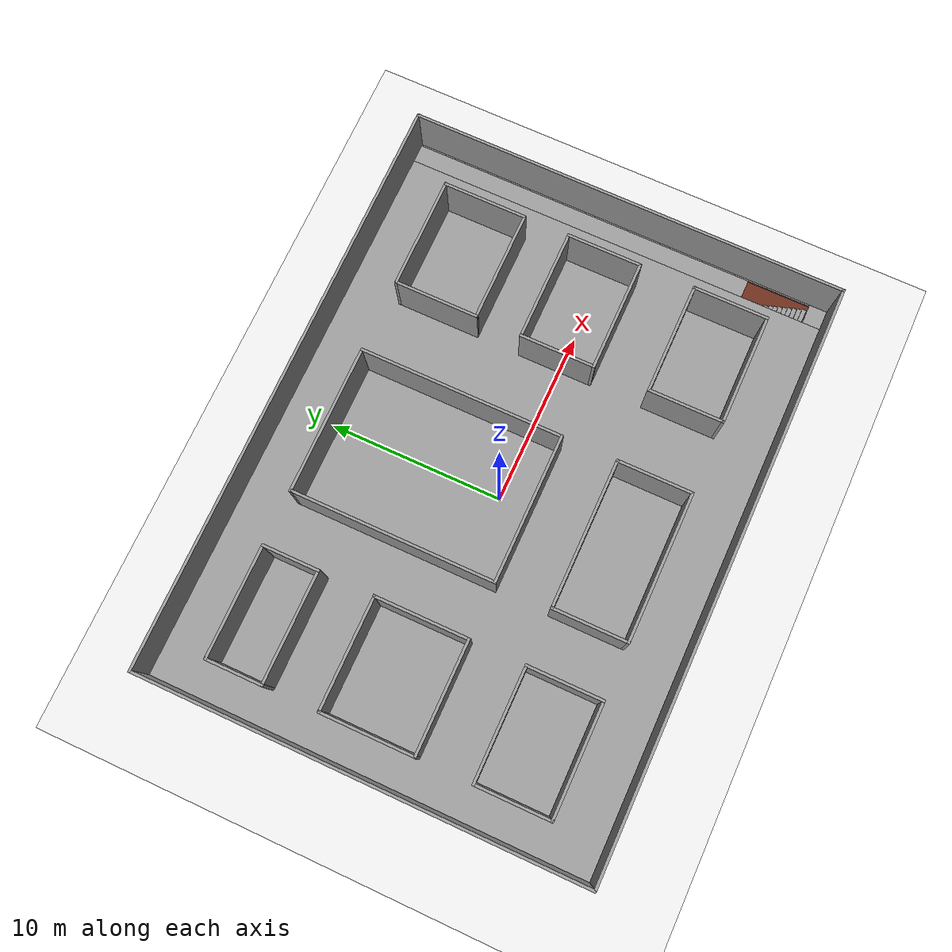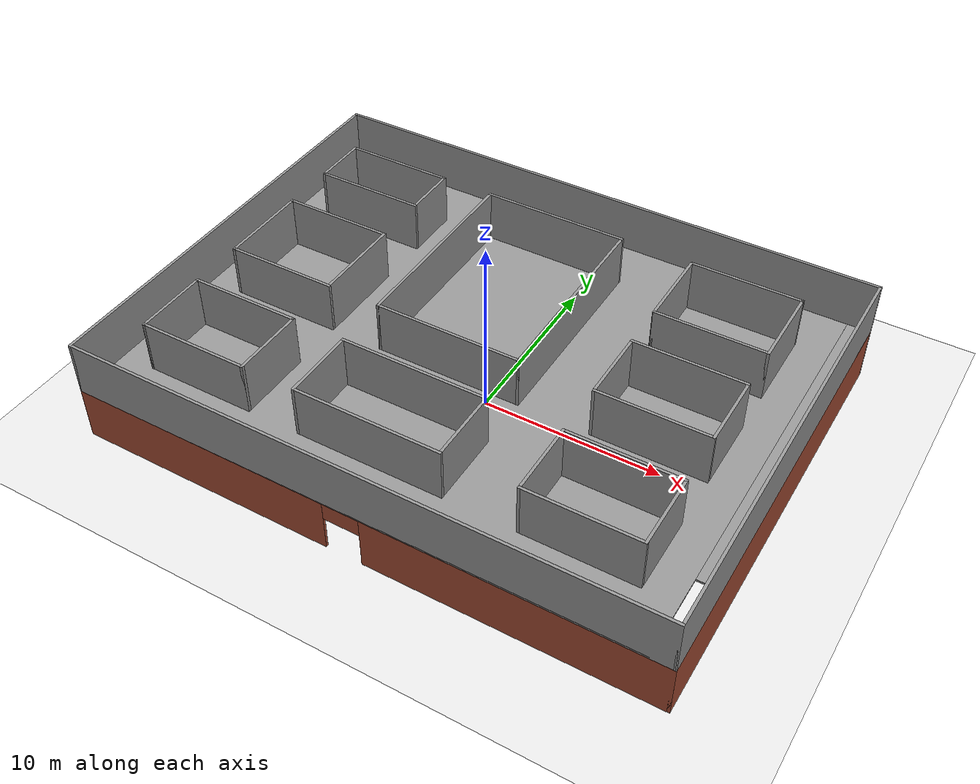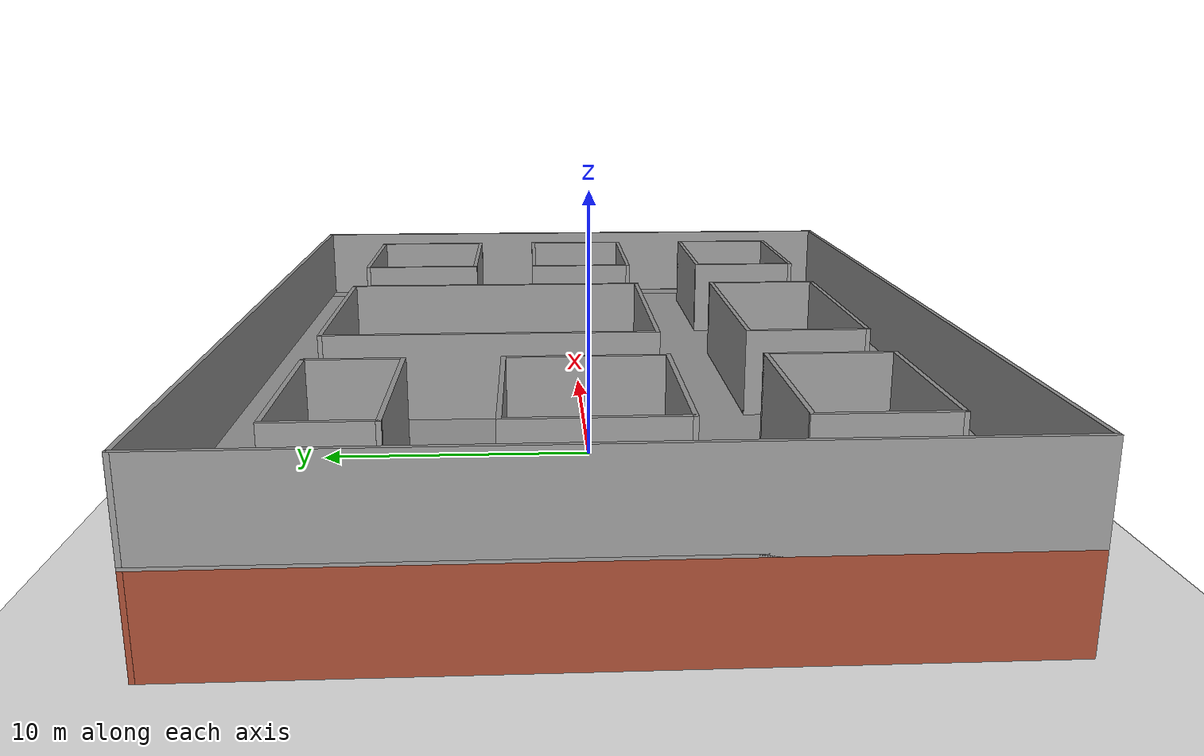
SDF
<sdf version="1.6">
 <world name="default">
  <light name="sun" type="directional">
   <pose>0 0 10 0 -0 0</pose>
   <diffuse>0.8 0.8 0.8 1</diffuse>
   <specular>0.2 0.2 0.2 1</specular>
   <attenuation>
    <range>1000</range>
    <constant>0.9</constant>
    <linear>0.01</linear>
    <quadratic>0.001</quadratic>
   </attenuation>
   <direction>-0.5 0.1 -0.9</direction>
  </light>
  <model name="ground_plane">
   <static>1</static>
   <link name="link">
    <collision name="collision">
     <geometry><plane><normal>0 0 1</normal><size>100 100</size></plane></geometry>
     <surface><friction><ode><mu>100</mu><mu2>50</mu2></ode></friction></surface>
    </collision>
    <visual name="visual">
     <cast_shadows>0</cast_shadows>
     <geometry><plane><normal>0 0 1</normal><size>100 100</size></plane></geometry>
     <material>
      <script><uri>file://media/materials/scripts/gazebo.material</uri><name>Gazebo/White</name></script>
     </material>
    </visual>
   </link>
  </model>
  <gravity>0 0 -9.8</gravity>
  <magnetic_field>6e-06 2.3e-05 -4.2e-05</magnetic_field>
  <atmosphere type="adiabatic"/>
  <physics name="default_physics" default="0" type="ode">
   <max_step_size>0.003</max_step_size>
   <real_time_factor>1.7</real_time_factor>
   <real_time_update_rate>1000</real_time_update_rate>
  </physics>
  <scene><ambient>0.4 0.4 0.4 1</ambient><background>0.7 0.7 0.7 1</background><shadows>1</shadows></scene>
  <model name="test_building">
   <link name="Door_3">
    <collision name="Door_3_Collision">
     <geometry><box><size>1 0.17 2</size></box></geometry>
     <pose>0 0 1 0 -0 0</pose>
    </collision>
    <visual name="Door_3_Visual">
     <pose>0 0 1 0 -0 0</pose>
     <geometry><box><size>1 0.17 2</size></box></geometry>
     <material>
      <script><uri>file://media/materials/scripts/gazebo.material</uri><name>Gazebo/Grey</name></script>
     </material>
    </visual>
    <pose>-11.0407 -2.12985 0 0 -0 0</pose>
   </link>
   <link name="Floor_0">
    <pose>0 0 3 0 -0 0</pose>
    <visual name="Floor_0_Visual_0">
     <pose>-0.613364 0 0.05 0 -0 0</pose>
     <geometry><box><size>30.9233 24.15 0.1</size></box></geometry>
     <material>
      <script><uri>file://media/materials/scripts/gazebo.material</uri><name>Gazebo/Grey</name></script>
      <ambient>1 1 1 1</ambient>
     </material>
     <meta><layer>1</layer></meta>
    </visual>
    <collision name="Floor_0_Collision_0">
     <geometry><box><size>30.9233 24.15 0.1</size></box></geometry>
     <pose>-0.613364 0 0.05 0 -0 0</pose>
    </collision>
    <visual name="Floor_0_Visual_1">
     <pose>15.4616 -11.5174 0.05 0 -0 0</pose>
     <geometry><box><size>1.22673 1.11518 0.1</size></box></geometry>
     <material>
      <script><uri>file://media/materials/scripts/gazebo.material</uri><name>Gazebo/Grey</name></script>
      <ambient>1 1 1 1</ambient>
     </material>
     <meta><layer>1</layer></meta>
    </visual>
    <collision name="Floor_0_Collision_1">
     <geometry><box><size>1.22673 1.11518 0.1</size></box></geometry>
     <pose>15.4616 -11.5174 0.05 0 -0 0</pose>
    </collision>
    <visual name="Floor_0_Visual_2">
     <pose>15.9616 0.557588 0.05 0 -0 0</pose>
     <geometry><box><size>0.226729 23.0348 0.1</size></box></geometry>
     <material>
      <script><uri>file://media/materials/scripts/gazebo.material</uri><name>Gazebo/Grey</name></script>
      <ambient>1 1 1 1</ambient>
     </material>
     <meta><layer>1</layer></meta>
    </visual>
    <collision name="Floor_0_Collision_2">
     <geometry><box><size>0.226729 23.0348 0.1</size></box></geometry>
     <pose>15.9616 0.557588 0.05 0 -0 0</pose>
    </collision>
    <visual name="Floor_0_Visual_3">
     <pose>15.3483 2.30759 0.05 0 -0 0</pose>
     <geometry><box><size>1 19.5348 0.1</size></box></geometry>
     <material>
      <script><uri>file://media/materials/scripts/gazebo.material</uri><name>Gazebo/Grey</name></script>
      <ambient>1 1 1 1</ambient>
     </material>
     <meta><layer>1</layer></meta>
    </visual>
    <collision name="Floor_0_Collision_3">
     <geometry><box><size>1 19.5348 0.1</size></box></geometry>
     <pose>15.3483 2.30759 0.05 0 -0 0</pose>
    </collision>
   </link>
   <link name="Stairs_1">
    <visual name="Stairs_1_Visual_0">
     <pose>15.3483 -7.57649 0.083333 0 -0 0</pose>
     <geometry><box><size>1 0.233333 0.166667</size></box></geometry>
     <material>
      <script><uri>file://media/materials/scripts/gazebo.material</uri><name>Gazebo/Grey</name></script>
      <ambient>1 1 1 1</ambient>
     </material>
     <meta><layer>0</layer></meta>
    </visual>
    <collision name="Stairs_1_Collision_0">
     <geometry><box><size>1 0.233333 0.166667</size></box></geometry>
     <pose>15.3483 -7.57649 0.083333 0 -0 0</pose>
    </collision>
    <visual name="Stairs_1_Visual_1">
     <pose>15.3483 -7.80982 0.25 0 -0 0</pose>
     <geometry><box><size>1 0.233333 0.166667</size></box></geometry>
     <material>
      <script><uri>file://media/materials/scripts/gazebo.material</uri><name>Gazebo/Grey</name></script>
      <ambient>1 1 1 1</ambient>
     </material>
     <meta><layer>0</layer></meta>
    </visual>
    <collision name="Stairs_1_Collision_1">
     <geometry><box><size>1 0.233333 0.166667</size></box></geometry>
     <pose>15.3483 -7.80982 0.25 0 -0 0</pose>
    </collision>
    <visual name="Stairs_1_Visual_2">
     <pose>15.3483 -8.04316 0.416667 0 -0 0</pose>
     <geometry><box><size>1 0.233333 0.166667</size></box></geometry>
     <material>
      <script><uri>file://media/materials/scripts/gazebo.material</uri><name>Gazebo/Grey</name></script>
      <ambient>1 1 1 1</ambient>
     </material>
     <meta><layer>0</layer></meta>
    </visual>
    <collision name="Stairs_1_Collision_2">
     <geometry><box><size>1 0.233333 0.166667</size></box></geometry>
     <pose>15.3483 -8.04316 0.416667 0 -0 0</pose>
    </collision>
    <visual name="Stairs_1_Visual_3">
     <pose>15.3483 -8.27649 0.583333 0 -0 0</pose>
     <geometry><box><size>1 0.233333 0.166667</size></box></geometry>
     <material>
      <script><uri>file://media/materials/scripts/gazebo.material</uri><name>Gazebo/Grey</name></script>
      <ambient>1 1 1 1</ambient>
     </material>
     <meta><layer>0</layer></meta>
    </visual>
    <collision name="Stairs_1_Collision_3">
     <geometry><box><size>1 0.233333 0.166667</size></box></geometry>
     <pose>15.3483 -8.27649 0.583333 0 -0 0</pose>
    </collision>
    <visual name="Stairs_1_Visual_4">
     <pose>15.3483 -8.50982 0.75 0 -0 0</pose>
     <geometry><box><size>1 0.233333 0.166667</size></box></geometry>
     <material>
      <script><uri>file://media/materials/scripts/gazebo.material</uri><name>Gazebo/Grey</name></script>
      <ambient>1 1 1 1</ambient>
     </material>
     <meta><layer>0</layer></meta>
    </visual>
    <collision name="Stairs_1_Collision_4">
     <geometry><box><size>1 0.233333 0.166667</size></box></geometry>
     <pose>15.3483 -8.50982 0.75 0 -0 0</pose>
    </collision>
    <visual name="Stairs_1_Visual_5">
     <pose>15.3483 -8.74316 0.916667 0 -0 0</pose>
     <geometry><box><size>1 0.233333 0.166667</size></box></geometry>
     <material>
      <script><uri>file://media/materials/scripts/gazebo.material</uri><name>Gazebo/Grey</name></script>
      <ambient>1 1 1 1</ambient>
     </material>
     <meta><layer>0</layer></meta>
    </visual>
    <collision name="Stairs_1_Collision_5">
     <geometry><box><size>1 0.233333 0.166667</size></box></geometry>
     <pose>15.3483 -8.74316 0.916667 0 -0 0</pose>
    </collision>
    <visual name="Stairs_1_Visual_6">
     <pose>15.3483 -8.97649 1.08333 0 -0 0</pose>
     <geometry><box><size>1 0.233333 0.166667</size></box></geometry>
     <material>
      <script><uri>file://media/materials/scripts/gazebo.material</uri><name>Gazebo/Grey</name></script>
      <ambient>1 1 1 1</ambient>
     </material>
     <meta><layer>0</layer></meta>
    </visual>
    <collision name="Stairs_1_Collision_6">
     <geometry><box><size>1 0.233333 0.166667</size></box></geometry>
     <pose>15.3483 -8.97649 1.08333 0 -0 0</pose>
    </collision>
    <visual name="Stairs_1_Visual_7">
     <pose>15.3483 -9.20983 1.25 0 -0 0</pose>
     <geometry><box><size>1 0.233333 0.166667</size></box></geometry>
     <material>
      <script><uri>file://media/materials/scripts/gazebo.material</uri><name>Gazebo/Grey</name></script>
      <ambient>1 1 1 1</ambient>
     </material>
     <meta><layer>0</layer></meta>
    </visual>
    <collision name="Stairs_1_Collision_7">
     <geometry><box><size>1 0.233333 0.166667</size></box></geometry>
     <pose>15.3483 -9.20983 1.25 0 -0 0</pose>
    </collision>
    <visual name="Stairs_1_Visual_8">
     <pose>15.3483 -9.44316 1.41667 0 -0 0</pose>
     <geometry><box><size>1 0.233333 0.166667</size></box></geometry>
     <material>
      <script><uri>file://media/materials/scripts/gazebo.material</uri><name>Gazebo/Grey</name></script>
      <ambient>1 1 1 1</ambient>
     </material>
     <meta><layer>0</layer></meta>
    </visual>
    <collision name="Stairs_1_Collision_8">
     <geometry><box><size>1 0.233333 0.166667</size></box></geometry>
     <pose>15.3483 -9.44316 1.41667 0 -0 0</pose>
    </collision>
    <visual name="Stairs_1_Visual_9">
     <pose>15.3483 -9.67649 1.58333 0 -0 0</pose>
     <geometry><box><size>1 0.233333 0.166667</size></box></geometry>
     <material>
      <script><uri>file://media/materials/scripts/gazebo.material</uri><name>Gazebo/Grey</name></script>
      <ambient>1 1 1 1</ambient>
     </material>
     <meta><layer>0</layer></meta>
    </visual>
    <collision name="Stairs_1_Collision_9">
     <geometry><box><size>1 0.233333 0.166667</size></box></geometry>
     <pose>15.3483 -9.67649 1.58333 0 -0 0</pose>
    </collision>
    <visual name="Stairs_1_Visual_10">
     <pose>15.3483 -9.90982 1.75 0 -0 0</pose>
     <geometry><box><size>1 0.233333 0.166667</size></box></geometry>
     <material>
      <script><uri>file://media/materials/scripts/gazebo.material</uri><name>Gazebo/Grey</name></script>
      <ambient>1 1 1 1</ambient>
     </material>
     <meta><layer>0</layer></meta>
    </visual>
    <collision name="Stairs_1_Collision_10">
     <geometry><box><size>1 0.233333 0.166667</size></box></geometry>
     <pose>15.3483 -9.90982 1.75 0 -0 0</pose>
    </collision>
    <visual name="Stairs_1_Visual_11">
     <pose>15.3483 -10.1432 1.91667 0 -0 0</pose>
     <geometry><box><size>1 0.233333 0.166667</size></box></geometry>
     <material>
      <script><uri>file://media/materials/scripts/gazebo.material</uri><name>Gazebo/Grey</name></script>
      <ambient>1 1 1 1</ambient>
     </material>
     <meta><layer>0</layer></meta>
    </visual>
    <collision name="Stairs_1_Collision_11">
     <geometry><box><size>1 0.233333 0.166667</size></box></geometry>
     <pose>15.3483 -10.1432 1.91667 0 -0 0</pose>
    </collision>
    <visual name="Stairs_1_Visual_12">
     <pose>15.3483 -10.3765 2.08333 0 -0 0</pose>
     <geometry><box><size>1 0.233333 0.166667</size></box></geometry>
     <material>
      <script><uri>file://media/materials/scripts/gazebo.material</uri><name>Gazebo/Grey</name></script>
      <ambient>1 1 1 1</ambient>
     </material>
     <meta><layer>0</layer></meta>
    </visual>
    <collision name="Stairs_1_Collision_12">
     <geometry><box><size>1 0.233333 0.166667</size></box></geometry>
     <pose>15.3483 -10.3765 2.08333 0 -0 0</pose>
    </collision>
    <visual name="Stairs_1_Visual_13">
     <pose>15.3483 -10.6098 2.25 0 -0 0</pose>
     <geometry><box><size>1 0.233333 0.166667</size></box></geometry>
     <material>
      <script><uri>file://media/materials/scripts/gazebo.material</uri><name>Gazebo/Grey</name></script>
      <ambient>1 1 1 1</ambient>
     </material>
     <meta><layer>0</layer></meta>
    </visual>
    <collision name="Stairs_1_Collision_13">
     <geometry><box><size>1 0.233333 0.166667</size></box></geometry>
     <pose>15.3483 -10.6098 2.25 0 -0 0</pose>
    </collision>
    <visual name="Stairs_1_Visual_14">
     <pose>15.3483 -10.8432 2.41667 0 -0 0</pose>
     <geometry><box><size>1 0.233333 0.166667</size></box></geometry>
     <material>
      <script><uri>file://media/materials/scripts/gazebo.material</uri><name>Gazebo/Grey</name></script>
      <ambient>1 1 1 1</ambient>
     </material>
     <meta><layer>0</layer></meta>
    </visual>
    <collision name="Stairs_1_Collision_14">
     <geometry><box><size>1 0.233333 0.166667</size></box></geometry>
     <pose>15.3483 -10.8432 2.41667 0 -0 0</pose>
    </collision>
   </link>
   <link name="Wall_0">
    <pose>0 -12 0 0 -0 0</pose>
    <visual name="Wall_0_Visual_0">
     <pose>-8.78811 0 1.5 0 -0 0</pose>
     <geometry><box><size>14.5738 0.15 3</size></box></geometry>
     <material>
      <script><uri>file://media/materials/scripts/gazebo.material</uri><name>Gazebo/Bricks</name></script>
      <ambient>1 1 1 1</ambient>
     </material>
     <meta><layer>0</layer></meta>
    </visual>
    <collision name="Wall_0_Collision_0">
     <geometry><box><size>14.5738 0.15 3</size></box></geometry>
     <pose>-8.78811 0 1.5 0 -0 0</pose>
    </collision>
    <visual name="Wall_0_Visual_1">
     <pose>8.28689 0 1.5 0 -0 0</pose>
     <geometry><box><size>15.5762 0.15 3</size></box></geometry>
     <material>
      <script><uri>file://media/materials/scripts/gazebo.material</uri><name>Gazebo/Bricks</name></script>
      <ambient>1 1 1 1</ambient>
     </material>
     <meta><layer>0</layer></meta>
    </visual>
    <collision name="Wall_0_Collision_1">
     <geometry><box><size>15.5762 0.15 3</size></box></geometry>
     <pose>8.28689 0 1.5 0 -0 0</pose>
    </collision>
    <visual name="Wall_0_Visual_2">
     <pose>-0.501223 0 2.5 0 -0 0</pose>
     <geometry><box><size>2 0.15 1</size></box></geometry>
     <material>
      <script><uri>file://media/materials/scripts/gazebo.material</uri><name>Gazebo/Bricks</name></script>
      <ambient>1 1 1 1</ambient>
     </material>
     <meta><layer>0</layer></meta>
    </visual>
    <collision name="Wall_0_Collision_2">
     <geometry><box><size>2 0.15 1</size></box></geometry>
     <pose>-0.501223 0 2.5 0 -0 0</pose>
    </collision>
   </link>
   <link name="Wall_1">
    <collision name="Wall_1_Collision">
     <geometry><box><size>24.15 0.15 3</size></box></geometry>
     <pose>0 0 1.5 0 -0 0</pose>
    </collision>
    <visual name="Wall_1_Visual">
     <pose>0 0 1.5 0 -0 0</pose>
     <geometry><box><size>24.15 0.15 3</size></box></geometry>
     <material>
      <script><uri>file://media/materials/scripts/gazebo.material</uri><name>Gazebo/Bricks</name></script>
      <ambient>1 1 1 1</ambient>
     </material>
     <meta><layer>0</layer></meta>
    </visual>
    <pose>16 0 0 0 -0 1.5708</pose>
   </link>
   <link name="Wall_10">
    <collision name="Wall_10_Collision">
     <geometry><box><size>6.15 0.15 3</size></box></geometry>
     <pose>0 0 1.5 0 -0 0</pose>
    </collision>
    <visual name="Wall_10_Visual">
     <pose>0 0 1.5 0 -0 0</pose>
     <geometry><box><size>6.15 0.15 3</size></box></geometry>
     <material>
      <script><uri>file://media/materials/scripts/gazebo.material</uri><name>Gazebo/Grey</name></script>
      <ambient>0.921569 0.807843 0.615686 1</ambient>
     </material>
     <meta><layer>0</layer></meta>
    </visual>
    <pose>-11 3 0 0 -0 0</pose>
   </link>
   <link name="Wall_11">
    <collision name="Wall_11_Collision">
     <geometry><box><size>5.15 0.15 3</size></box></geometry>
     <pose>0 0 1.5 0 -0 0</pose>
    </collision>
    <visual name="Wall_11_Visual">
     <pose>0 0 1.5 0 -0 0</pose>
     <geometry><box><size>5.15 0.15 3</size></box></geometry>
     <material>
      <script><uri>file://media/materials/scripts/gazebo.material</uri><name>Gazebo/Grey</name></script>
      <ambient>0.921569 0.807843 0.615686 1</ambient>
     </material>
     <meta><layer>0</layer></meta>
    </visual>
    <pose>-8 0.5 0 0 -0 -1.5708</pose>
   </link>
   <link name="Wall_12">
    <collision name="Wall_12_Collision">
     <geometry><box><size>6.15 0.15 3</size></box></geometry>
     <pose>0 0 1.5 0 -0 0</pose>
    </collision>
    <visual name="Wall_12_Visual">
     <pose>0 0 1.5 0 -0 0</pose>
     <geometry><box><size>6.15 0.15 3</size></box></geometry>
     <material>
      <script><uri>file://media/materials/scripts/gazebo.material</uri><name>Gazebo/Grey</name></script>
      <ambient>0.921569 0.807843 0.615686 1</ambient>
     </material>
     <meta><layer>0</layer></meta>
    </visual>
    <pose>-11 -2 0 0 -0 3.14159</pose>
   </link>
   <link name="Wall_13">
    <collision name="Wall_13_Collision">
     <geometry><box><size>5.15 0.15 3</size></box></geometry>
     <pose>0 0 1.5 0 -0 0</pose>
    </collision>
    <visual name="Wall_13_Visual">
     <pose>0 0 1.5 0 -0 0</pose>
     <geometry><box><size>5.15 0.15 3</size></box></geometry>
     <material>
      <script><uri>file://media/materials/scripts/gazebo.material</uri><name>Gazebo/Grey</name></script>
      <ambient>0.921569 0.807843 0.615686 1</ambient>
     </material>
     <meta><layer>0</layer></meta>
    </visual>
    <pose>-14 0.5 0 0 -0 1.5708</pose>
   </link>
   <link name="Wall_15">
    <pose>-11 -5 0 0 -0 0</pose>
    <visual name="Wall_15_Visual_0">
     <pose>-1.78775 0 1.5 0 -0 0</pose>
     <geometry><box><size>2.57449 0.15 3</size></box></geometry>
     <material>
      <script><uri>file://media/materials/scripts/gazebo.material</uri><name>Gazebo/Grey</name></script>
      <ambient>0.921569 0.807843 0.615686 1</ambient>
     </material>
     <meta><layer>0</layer></meta>
    </visual>
    <collision name="Wall_15_Collision_0">
     <geometry><box><size>2.57449 0.15 3</size></box></geometry>
     <pose>-1.78775 0 1.5 0 -0 0</pose>
    </collision>
    <visual name="Wall_15_Visual_1">
     <pose>1.78725 0 1.5 0 -0 0</pose>
     <geometry><box><size>2.57551 0.15 3</size></box></geometry>
     <material>
      <script><uri>file://media/materials/scripts/gazebo.material</uri><name>Gazebo/Grey</name></script>
      <ambient>0.921569 0.807843 0.615686 1</ambient>
     </material>
     <meta><layer>0</layer></meta>
    </visual>
    <collision name="Wall_15_Collision_1">
     <geometry><box><size>2.57551 0.15 3</size></box></geometry>
     <pose>1.78725 0 1.5 0 -0 0</pose>
    </collision>
    <visual name="Wall_15_Visual_2">
     <pose>-0.000507 0 2.5 0 -0 0</pose>
     <geometry><box><size>1 0.15 1</size></box></geometry>
     <material>
      <script><uri>file://media/materials/scripts/gazebo.material</uri><name>Gazebo/Grey</name></script>
      <ambient>0.921569 0.807843 0.615686 1</ambient>
     </material>
     <meta><layer>0</layer></meta>
    </visual>
    <collision name="Wall_15_Collision_2">
     <geometry><box><size>1 0.15 1</size></box></geometry>
     <pose>-0.000507 0 2.5 0 -0 0</pose>
    </collision>
   </link>
   <link name="Wall_16">
    <collision name="Wall_16_Collision">
     <geometry><box><size>4.15 0.15 3</size></box></geometry>
     <pose>0 0 1.5 0 -0 0</pose>
    </collision>
    <visual name="Wall_16_Visual">
     <pose>0 0 1.5 0 -0 0</pose>
     <geometry><box><size>4.15 0.15 3</size></box></geometry>
     <material>
      <script><uri>file://media/materials/scripts/gazebo.material</uri><name>Gazebo/Grey</name></script>
      <ambient>0.921569 0.807843 0.615686 1</ambient>
     </material>
     <meta><layer>0</layer></meta>
    </visual>
    <pose>-8 -7 0 0 -0 -1.5708</pose>
   </link>
   <link name="Wall_18">
    <collision name="Wall_18_Collision">
     <geometry><box><size>4.15 0.15 3</size></box></geometry>
     <pose>0 0 1.5 0 -0 0</pose>
    </collision>
    <visual name="Wall_18_Visual">
     <pose>0 0 1.5 0 -0 0</pose>
     <geometry><box><size>4.15 0.15 3</size></box></geometry>
     <material>
      <script><uri>file://media/materials/scripts/gazebo.material</uri><name>Gazebo/Grey</name></script>
      <ambient>0.921569 0.807843 0.615686 1</ambient>
     </material>
     <meta><layer>0</layer></meta>
    </visual>
    <pose>-14 -7 0 0 -0 1.5708</pose>
   </link>
   <link name="Wall_2">
    <collision name="Wall_2_Collision">
     <geometry><box><size>32.15 0.15 3</size></box></geometry>
     <pose>0 0 1.5 0 -0 0</pose>
    </collision>
    <visual name="Wall_2_Visual">
     <pose>0 0 1.5 0 -0 0</pose>
     <geometry><box><size>32.15 0.15 3</size></box></geometry>
     <material>
      <script><uri>file://media/materials/scripts/gazebo.material</uri><name>Gazebo/Bricks</name></script>
      <ambient>1 1 1 1</ambient>
     </material>
     <meta><layer>0</layer></meta>
    </visual>
    <pose>0 12 0 0 -0 3.14159</pose>
   </link>
   <link name="Wall_20">
    <collision name="Wall_20_Collision">
     <geometry><box><size>11.15 0.15 3</size></box></geometry>
     <pose>0 0 1.5 0 -0 0</pose>
    </collision>
    <visual name="Wall_20_Visual">
     <pose>0 0 1.5 0 -0 0</pose>
     <geometry><box><size>11.15 0.15 3</size></box></geometry>
     <material>
      <script><uri>file://media/materials/scripts/gazebo.material</uri><name>Gazebo/CeilingTiled</name></script>
      <ambient>0.435294 0.796078 0.67451 1</ambient>
     </material>
     <meta><layer>0</layer></meta>
    </visual>
    <pose>-5 3.5 0 0 -0 -1.5708</pose>
   </link>
   <link name="Wall_21">
    <pose>-1 -2 0 0 -0 0</pose>
    <visual name="Wall_21_Visual_0">
     <pose>-2.21913 0 1.5 0 -0 0</pose>
     <geometry><box><size>3.71173 0.15 3</size></box></geometry>
     <material>
      <script><uri>file://media/materials/scripts/gazebo.material</uri><name>Gazebo/CeilingTiled</name></script>
      <ambient>0.435294 0.796078 0.67451 1</ambient>
     </material>
     <meta><layer>0</layer></meta>
    </visual>
    <collision name="Wall_21_Collision_0">
     <geometry><box><size>3.71173 0.15 3</size></box></geometry>
     <pose>-2.21913 0 1.5 0 -0 0</pose>
    </collision>
    <visual name="Wall_21_Visual_1">
     <pose>2.35587 0 1.5 0 -0 0</pose>
     <geometry><box><size>3.43827 0.15 3</size></box></geometry>
     <material>
      <script><uri>file://media/materials/scripts/gazebo.material</uri><name>Gazebo/CeilingTiled</name></script>
      <ambient>0.435294 0.796078 0.67451 1</ambient>
     </material>
     <meta><layer>0</layer></meta>
    </visual>
    <collision name="Wall_21_Collision_1">
     <geometry><box><size>3.43827 0.15 3</size></box></geometry>
     <pose>2.35587 0 1.5 0 -0 0</pose>
    </collision>
    <visual name="Wall_21_Visual_2">
     <pose>0.136732 0 2.5 0 -0 0</pose>
     <geometry><box><size>1 0.15 1</size></box></geometry>
     <material>
      <script><uri>file://media/materials/scripts/gazebo.material</uri><name>Gazebo/CeilingTiled</name></script>
      <ambient>0.435294 0.796078 0.67451 1</ambient>
     </material>
     <meta><layer>0</layer></meta>
    </visual>
    <collision name="Wall_21_Collision_2">
     <geometry><box><size>1 0.15 1</size></box></geometry>
     <pose>0.136732 0 2.5 0 -0 0</pose>
    </collision>
   </link>
   <link name="Wall_22">
    <collision name="Wall_22_Collision">
     <geometry><box><size>11.15 0.15 3</size></box></geometry>
     <pose>0 0 1.5 0 -0 0</pose>
    </collision>
    <visual name="Wall_22_Visual">
     <pose>0 0 1.5 0 -0 0</pose>
     <geometry><box><size>11.15 0.15 3</size></box></geometry>
     <material>
      <script><uri>file://media/materials/scripts/gazebo.material</uri><name>Gazebo/CeilingTiled</name></script>
      <ambient>0.435294 0.796078 0.67451 1</ambient>
     </material>
     <meta><layer>0</layer></meta>
    </visual>
    <pose>3 3.5 0 0 -0 1.5708</pose>
   </link>
   <link name="Wall_23">
    <pose>-1 9 0 0 -0 3.14159</pose>
    <visual name="Wall_23_Visual_0">
     <pose>-2.29553 0 1.5 0 -0 0</pose>
     <geometry><box><size>3.55895 0.15 3</size></box></geometry>
     <material>
      <script><uri>file://media/materials/scripts/gazebo.material</uri><name>Gazebo/CeilingTiled</name></script>
      <ambient>0.435294 0.796078 0.67451 1</ambient>
     </material>
     <meta><layer>0</layer></meta>
    </visual>
    <collision name="Wall_23_Collision_0">
     <geometry><box><size>3.55895 0.15 3</size></box></geometry>
     <pose>-2.29553 0 1.5 0 -0 0</pose>
    </collision>
    <visual name="Wall_23_Visual_1">
     <pose>2.27948 0 1.5 0 -0 0</pose>
     <geometry><box><size>3.59105 0.15 3</size></box></geometry>
     <material>
      <script><uri>file://media/materials/scripts/gazebo.material</uri><name>Gazebo/CeilingTiled</name></script>
      <ambient>0.435294 0.796078 0.67451 1</ambient>
     </material>
     <meta><layer>0</layer></meta>
    </visual>
    <collision name="Wall_23_Collision_1">
     <geometry><box><size>3.59105 0.15 3</size></box></geometry>
     <pose>2.27948 0 1.5 0 -0 0</pose>
    </collision>
    <visual name="Wall_23_Visual_2">
     <pose>-0.016051 0 2.5 0 -0 0</pose>
     <geometry><box><size>1 0.15 1</size></box></geometry>
     <material>
      <script><uri>file://media/materials/scripts/gazebo.material</uri><name>Gazebo/CeilingTiled</name></script>
      <ambient>0.435294 0.796078 0.67451 1</ambient>
     </material>
     <meta><layer>0</layer></meta>
    </visual>
    <collision name="Wall_23_Collision_2">
     <geometry><box><size>1 0.15 1</size></box></geometry>
     <pose>-0.016051 0 2.5 0 -0 0</pose>
    </collision>
   </link>
   <link name="Wall_25">
    <collision name="Wall_25_Collision">
     <geometry><box><size>8.15 0.15 3</size></box></geometry>
     <pose>0 0 1.5 0 -0 0</pose>
    </collision>
    <visual name="Wall_25_Visual">
     <pose>0 0 1.5 0 -0 0</pose>
     <geometry><box><size>8.15 0.15 3</size></box></geometry>
     <material>
      <script><uri>file://media/materials/scripts/gazebo.material</uri><name>Gazebo/CeilingTiled</name></script>
      <ambient>0.435294 0.796078 0.67451 1</ambient>
     </material>
     <meta><layer>0</layer></meta>
    </visual>
    <pose>-1 -5 0 0 -0 0</pose>
   </link>
   <link name="Wall_26">
    <collision name="Wall_26_Collision">
     <geometry><box><size>4.15 0.15 3</size></box></geometry>
     <pose>0 0 1.5 0 -0 0</pose>
    </collision>
    <visual name="Wall_26_Visual">
     <pose>0 0 1.5 0 -0 0</pose>
     <geometry><box><size>4.15 0.15 3</size></box></geometry>
     <material>
      <script><uri>file://media/materials/scripts/gazebo.material</uri><name>Gazebo/CeilingTiled</name></script>
      <ambient>0.435294 0.796078 0.67451 1</ambient>
     </material>
     <meta><layer>0</layer></meta>
    </visual>
    <pose>3 -7 0 0 -0 -1.5708</pose>
   </link>
   <link name="Wall_27">
    <pose>-1 -9 0 0 -0 3.14159</pose>
    <visual name="Wall_27_Visual_0">
     <pose>-2.33575 0 1.5 0 -0 0</pose>
     <geometry><box><size>3.4785 0.15 3</size></box></geometry>
     <material>
      <script><uri>file://media/materials/scripts/gazebo.material</uri><name>Gazebo/CeilingTiled</name></script>
      <ambient>0.435294 0.796078 0.67451 1</ambient>
     </material>
     <meta><layer>0</layer></meta>
    </visual>
    <collision name="Wall_27_Collision_0">
     <geometry><box><size>3.4785 0.15 3</size></box></geometry>
     <pose>-2.33575 0 1.5 0 -0 0</pose>
    </collision>
    <visual name="Wall_27_Visual_1">
     <pose>2.23925 0 1.5 0 -0 0</pose>
     <geometry><box><size>3.6715 0.15 3</size></box></geometry>
     <material>
      <script><uri>file://media/materials/scripts/gazebo.material</uri><name>Gazebo/CeilingTiled</name></script>
      <ambient>0.435294 0.796078 0.67451 1</ambient>
     </material>
     <meta><layer>0</layer></meta>
    </visual>
    <collision name="Wall_27_Collision_1">
     <geometry><box><size>3.6715 0.15 3</size></box></geometry>
     <pose>2.23925 0 1.5 0 -0 0</pose>
    </collision>
    <visual name="Wall_27_Visual_2">
     <pose>-0.096505 0 2.5 0 -0 0</pose>
     <geometry><box><size>1 0.15 1</size></box></geometry>
     <material>
      <script><uri>file://media/materials/scripts/gazebo.material</uri><name>Gazebo/CeilingTiled</name></script>
      <ambient>0.435294 0.796078 0.67451 1</ambient>
     </material>
     <meta><layer>0</layer></meta>
    </visual>
    <collision name="Wall_27_Collision_2">
     <geometry><box><size>1 0.15 1</size></box></geometry>
     <pose>-0.096505 0 2.5 0 -0 0</pose>
    </collision>
   </link>
   <link name="Wall_28">
    <collision name="Wall_28_Collision">
     <geometry><box><size>4.15 0.15 3</size></box></geometry>
     <pose>0 0 1.5 0 -0 0</pose>
    </collision>
    <visual name="Wall_28_Visual">
     <pose>0 0 1.5 0 -0 0</pose>
     <geometry><box><size>4.15 0.15 3</size></box></geometry>
     <material>
      <script><uri>file://media/materials/scripts/gazebo.material</uri><name>Gazebo/CeilingTiled</name></script>
      <ambient>0.435294 0.796078 0.67451 1</ambient>
     </material>
     <meta><layer>0</layer></meta>
    </visual>
    <pose>-5 -7 0 0 -0 1.5708</pose>
   </link>
   <link name="Wall_3">
    <collision name="Wall_3_Collision">
     <geometry><box><size>24.15 0.15 3</size></box></geometry>
     <pose>0 0 1.5 0 -0 0</pose>
    </collision>
    <visual name="Wall_3_Visual">
     <pose>0 0 1.5 0 -0 0</pose>
     <geometry><box><size>24.15 0.15 3</size></box></geometry>
     <material>
      <script><uri>file://media/materials/scripts/gazebo.material</uri><name>Gazebo/Bricks</name></script>
      <ambient>1 1 1 1</ambient>
     </material>
     <meta><layer>0</layer></meta>
    </visual>
    <pose>-16 0 0 0 -0 -1.5708</pose>
   </link>
   <link name="Wall_30">
    <collision name="Wall_30_Collision">
     <geometry><box><size>4.65 0.15 3</size></box></geometry>
     <pose>0 0 1.5 0 -0 0</pose>
    </collision>
    <visual name="Wall_30_Visual">
     <pose>0 0 1.5 0 -0 0</pose>
     <geometry><box><size>4.65 0.15 3</size></box></geometry>
     <material>
      <script><uri>file://media/materials/scripts/gazebo.material</uri><name>Gazebo/CeilingTiled</name></script>
      <ambient>1 1 1 1</ambient>
     </material>
     <meta><layer>0</layer></meta>
    </visual>
    <pose>7 6.75 0 0 -0 -1.5708</pose>
   </link>
   <link name="Wall_31">
    <pose>10 4.5 0 0 -0 0</pose>
    <visual name="Wall_31_Visual_0">
     <pose>-1.70802 0 1.5 0 -0 0</pose>
     <geometry><box><size>2.73397 0.15 3</size></box></geometry>
     <material>
      <script><uri>file://media/materials/scripts/gazebo.material</uri><name>Gazebo/CeilingTiled</name></script>
      <ambient>1 1 1 1</ambient>
     </material>
     <meta><layer>0</layer></meta>
    </visual>
    <collision name="Wall_31_Collision_0">
     <geometry><box><size>2.73397 0.15 3</size></box></geometry>
     <pose>-1.70802 0 1.5 0 -0 0</pose>
    </collision>
    <visual name="Wall_31_Visual_1">
     <pose>1.86698 0 1.5 0 -0 0</pose>
     <geometry><box><size>2.41603 0.15 3</size></box></geometry>
     <material>
      <script><uri>file://media/materials/scripts/gazebo.material</uri><name>Gazebo/CeilingTiled</name></script>
      <ambient>1 1 1 1</ambient>
     </material>
     <meta><layer>0</layer></meta>
    </visual>
    <collision name="Wall_31_Collision_1">
     <geometry><box><size>2.41603 0.15 3</size></box></geometry>
     <pose>1.86698 0 1.5 0 -0 0</pose>
    </collision>
    <visual name="Wall_31_Visual_2">
     <pose>0.15897 0 2.5 0 -0 0</pose>
     <geometry><box><size>1 0.15 1</size></box></geometry>
     <material>
      <script><uri>file://media/materials/scripts/gazebo.material</uri><name>Gazebo/CeilingTiled</name></script>
      <ambient>1 1 1 1</ambient>
     </material>
     <meta><layer>0</layer></meta>
    </visual>
    <collision name="Wall_31_Collision_2">
     <geometry><box><size>1 0.15 1</size></box></geometry>
     <pose>0.15897 0 2.5 0 -0 0</pose>
    </collision>
   </link>
   <link name="Wall_32">
    <collision name="Wall_32_Collision">
     <geometry><box><size>4.65 0.15 3</size></box></geometry>
     <pose>0 0 1.5 0 -0 0</pose>
    </collision>
    <visual name="Wall_32_Visual">
     <pose>0 0 1.5 0 -0 0</pose>
     <geometry><box><size>4.65 0.15 3</size></box></geometry>
     <material>
      <script><uri>file://media/materials/scripts/gazebo.material</uri><name>Gazebo/CeilingTiled</name></script>
      <ambient>1 1 1 1</ambient>
     </material>
     <meta><layer>0</layer></meta>
    </visual>
    <pose>13 6.75 0 0 -0 1.5708</pose>
   </link>
   <link name="Wall_33">
    <collision name="Wall_33_Collision">
     <geometry><box><size>6.15 0.15 3</size></box></geometry>
     <pose>0 0 1.5 0 -0 0</pose>
    </collision>
    <visual name="Wall_33_Visual">
     <pose>0 0 1.5 0 -0 0</pose>
     <geometry><box><size>6.15 0.15 3</size></box></geometry>
     <material>
      <script><uri>file://media/materials/scripts/gazebo.material</uri><name>Gazebo/CeilingTiled</name></script>
      <ambient>1 1 1 1</ambient>
     </material>
     <meta><layer>0</layer></meta>
    </visual>
    <pose>10 9 0 0 -0 3.14159</pose>
   </link>
   <link name="Wall_35">
    <collision name="Wall_35_Collision">
     <geometry><box><size>6.15 0.15 3</size></box></geometry>
     <pose>0 0 1.5 0 -0 0</pose>
    </collision>
    <visual name="Wall_35_Visual">
     <pose>0 0 1.5 0 -0 0</pose>
     <geometry><box><size>6.15 0.15 3</size></box></geometry>
     <material>
      <script><uri>file://media/materials/scripts/gazebo.material</uri><name>Gazebo/CeilingTiled</name></script>
      <ambient>1 1 1 1</ambient>
     </material>
     <meta><layer>0</layer></meta>
    </visual>
    <pose>10 2 0 0 -0 0</pose>
   </link>
   <link name="Wall_36">
    <collision name="Wall_36_Collision">
     <geometry><box><size>4.15 0.15 3</size></box></geometry>
     <pose>0 0 1.5 0 -0 0</pose>
    </collision>
    <visual name="Wall_36_Visual">
     <pose>0 0 1.5 0 -0 0</pose>
     <geometry><box><size>4.15 0.15 3</size></box></geometry>
     <material>
      <script><uri>file://media/materials/scripts/gazebo.material</uri><name>Gazebo/CeilingTiled</name></script>
      <ambient>1 1 1 1</ambient>
     </material>
     <meta><layer>0</layer></meta>
    </visual>
    <pose>13 0 0 0 -0 -1.5708</pose>
   </link>
   <link name="Wall_37">
    <pose>10 -2 0 0 -0 3.14159</pose>
    <visual name="Wall_37_Visual_0">
     <pose>-1.80664 0 1.5 0 -0 0</pose>
     <geometry><box><size>2.53671 0.15 3</size></box></geometry>
     <material>
      <script><uri>file://media/materials/scripts/gazebo.material</uri><name>Gazebo/CeilingTiled</name></script>
      <ambient>1 1 1 1</ambient>
     </material>
     <meta><layer>0</layer></meta>
    </visual>
    <collision name="Wall_37_Collision_0">
     <geometry><box><size>2.53671 0.15 3</size></box></geometry>
     <pose>-1.80664 0 1.5 0 -0 0</pose>
    </collision>
    <visual name="Wall_37_Visual_1">
     <pose>1.76836 0 1.5 0 -0 0</pose>
     <geometry><box><size>2.61329 0.15 3</size></box></geometry>
     <material>
      <script><uri>file://media/materials/scripts/gazebo.material</uri><name>Gazebo/CeilingTiled</name></script>
      <ambient>1 1 1 1</ambient>
     </material>
     <meta><layer>0</layer></meta>
    </visual>
    <collision name="Wall_37_Collision_1">
     <geometry><box><size>2.61329 0.15 3</size></box></geometry>
     <pose>1.76836 0 1.5 0 -0 0</pose>
    </collision>
    <visual name="Wall_37_Visual_2">
     <pose>-0.038288 0 2.5 0 -0 0</pose>
     <geometry><box><size>1 0.15 1</size></box></geometry>
     <material>
      <script><uri>file://media/materials/scripts/gazebo.material</uri><name>Gazebo/CeilingTiled</name></script>
      <ambient>1 1 1 1</ambient>
     </material>
     <meta><layer>0</layer></meta>
    </visual>
    <collision name="Wall_37_Collision_2">
     <geometry><box><size>1 0.15 1</size></box></geometry>
     <pose>-0.038288 0 2.5 0 -0 0</pose>
    </collision>
   </link>
   <link name="Wall_38">
    <collision name="Wall_38_Collision">
     <geometry><box><size>4.15 0.15 3</size></box></geometry>
     <pose>0 0 1.5 0 -0 0</pose>
    </collision>
    <visual name="Wall_38_Visual">
     <pose>0 0 1.5 0 -0 0</pose>
     <geometry><box><size>4.15 0.15 3</size></box></geometry>
     <material>
      <script><uri>file://media/materials/scripts/gazebo.material</uri><name>Gazebo/CeilingTiled</name></script>
      <ambient>1 1 1 1</ambient>
     </material>
     <meta><layer>0</layer></meta>
    </visual>
    <pose>7 0 0 0 -0 1.5708</pose>
   </link>
   <link name="Wall_40">
    <pose>10 -5 0 0 -0 0</pose>
    <visual name="Wall_40_Visual_0">
     <pose>-1.74824 0 1.5 0 -0 0</pose>
     <geometry><box><size>2.65352 0.15 3</size></box></geometry>
     <material>
      <script><uri>file://media/materials/scripts/gazebo.material</uri><name>Gazebo/CeilingTiled</name></script>
      <ambient>1 1 1 1</ambient>
     </material>
     <meta><layer>0</layer></meta>
    </visual>
    <collision name="Wall_40_Collision_0">
     <geometry><box><size>2.65352 0.15 3</size></box></geometry>
     <pose>-1.74824 0 1.5 0 -0 0</pose>
    </collision>
    <visual name="Wall_40_Visual_1">
     <pose>1.82676 0 1.5 0 -0 0</pose>
     <geometry><box><size>2.49648 0.15 3</size></box></geometry>
     <material>
      <script><uri>file://media/materials/scripts/gazebo.material</uri><name>Gazebo/CeilingTiled</name></script>
      <ambient>1 1 1 1</ambient>
     </material>
     <meta><layer>0</layer></meta>
    </visual>
    <collision name="Wall_40_Collision_1">
     <geometry><box><size>2.49648 0.15 3</size></box></geometry>
     <pose>1.82676 0 1.5 0 -0 0</pose>
    </collision>
    <visual name="Wall_40_Visual_2">
     <pose>0.078515 0 2.5 0 -0 0</pose>
     <geometry><box><size>1 0.15 1</size></box></geometry>
     <material>
      <script><uri>file://media/materials/scripts/gazebo.material</uri><name>Gazebo/CeilingTiled</name></script>
      <ambient>1 1 1 1</ambient>
     </material>
     <meta><layer>0</layer></meta>
    </visual>
    <collision name="Wall_40_Collision_2">
     <geometry><box><size>1 0.15 1</size></box></geometry>
     <pose>0.078515 0 2.5 0 -0 0</pose>
    </collision>
   </link>
   <link name="Wall_41">
    <collision name="Wall_41_Collision">
     <geometry><box><size>4.15 0.15 3</size></box></geometry>
     <pose>0 0 1.5 0 -0 0</pose>
    </collision>
    <visual name="Wall_41_Visual">
     <pose>0 0 1.5 0 -0 0</pose>
     <geometry><box><size>4.15 0.15 3</size></box></geometry>
     <material>
      <script><uri>file://media/materials/scripts/gazebo.material</uri><name>Gazebo/CeilingTiled</name></script>
      <ambient>1 1 1 1</ambient>
     </material>
     <meta><layer>0</layer></meta>
    </visual>
    <pose>13 -7 0 0 -0 -1.5708</pose>
   </link>
   <link name="Wall_42">
    <collision name="Wall_42_Collision">
     <geometry><box><size>6.15 0.15 3</size></box></geometry>
     <pose>0 0 1.5 0 -0 0</pose>
    </collision>
    <visual name="Wall_42_Visual">
     <pose>0 0 1.5 0 -0 0</pose>
     <geometry><box><size>6.15 0.15 3</size></box></geometry>
     <material>
      <script><uri>file://media/materials/scripts/gazebo.material</uri><name>Gazebo/CeilingTiled</name></script>
      <ambient>1 1 1 1</ambient>
     </material>
     <meta><layer>0</layer></meta>
    </visual>
    <pose>10 -9 0 0 -0 3.14159</pose>
   </link>
   <link name="Wall_43">
    <collision name="Wall_43_Collision">
     <geometry><box><size>4.15 0.15 3</size></box></geometry>
     <pose>0 0 1.5 0 -0 0</pose>
    </collision>
    <visual name="Wall_43_Visual">
     <pose>0 0 1.5 0 -0 0</pose>
     <geometry><box><size>4.15 0.15 3</size></box></geometry>
     <material>
      <script><uri>file://media/materials/scripts/gazebo.material</uri><name>Gazebo/CeilingTiled</name></script>
      <ambient>1 1 1 1</ambient>
     </material>
     <meta><layer>0</layer></meta>
    </visual>
    <pose>7 -7 0 0 -0 1.5708</pose>
   </link>
   <link name="Wall_45">
    <collision name="Wall_45_Collision">
     <geometry><box><size>6.15 0.15 3</size></box></geometry>
     <pose>0 0 1.5 0 -0 0</pose>
    </collision>
    <visual name="Wall_45_Visual">
     <pose>0 0 1.5 0 -0 0</pose>
     <geometry><box><size>6.15 0.15 3</size></box></geometry>
     <material>
      <script><uri>file://media/materials/scripts/gazebo.material</uri><name>Gazebo/Grey</name></script>
      <ambient>0.921569 0.807843 0.615686 1</ambient>
     </material>
     <meta><layer>0</layer></meta>
    </visual>
    <pose>-11 -9 0 0 -0 0</pose>
   </link>
   <link name="Wall_47">
    <collision name="Wall_47_Collision">
     <geometry><box><size>32.15 0.15 3</size></box></geometry>
     <pose>0 0 1.5 0 -0 0</pose>
    </collision>
    <visual name="Wall_47_Visual">
     <pose>0 0 1.5 0 -0 0</pose>
     <geometry><box><size>32.15 0.15 3</size></box></geometry>
     <material>
      <script><uri>file://media/materials/scripts/gazebo.material</uri><name>Gazebo/Grey</name></script>
      <ambient>1 1 1 1</ambient>
     </material>
     <meta><layer>1</layer></meta>
    </visual>
    <pose>0 -12 3 0 -0 0</pose>
   </link>
   <link name="Wall_48">
    <collision name="Wall_48_Collision">
     <geometry><box><size>24.15 0.15 3</size></box></geometry>
     <pose>0 0 1.5 0 -0 0</pose>
    </collision>
    <visual name="Wall_48_Visual">
     <pose>0 0 1.5 0 -0 0</pose>
     <geometry><box><size>24.15 0.15 3</size></box></geometry>
     <material>
      <script><uri>file://media/materials/scripts/gazebo.material</uri><name>Gazebo/Grey</name></script>
      <ambient>1 1 1 1</ambient>
     </material>
     <meta><layer>1</layer></meta>
    </visual>
    <pose>16 0 3 0 -0 1.5708</pose>
   </link>
   <link name="Wall_49">
    <collision name="Wall_49_Collision">
     <geometry><box><size>32.15 0.15 3</size></box></geometry>
     <pose>0 0 1.5 0 -0 0</pose>
    </collision>
    <visual name="Wall_49_Visual">
     <pose>0 0 1.5 0 -0 0</pose>
     <geometry><box><size>32.15 0.15 3</size></box></geometry>
     <material>
      <script><uri>file://media/materials/scripts/gazebo.material</uri><name>Gazebo/Grey</name></script>
      <ambient>1 1 1 1</ambient>
     </material>
     <meta><layer>1</layer></meta>
    </visual>
    <pose>0 12 3 0 -0 3.14159</pose>
   </link>
   <link name="Wall_5">
    <collision name="Wall_5_Collision">
     <geometry><box><size>6.15 0.15 3</size></box></geometry>
     <pose>0 0 1.5 0 -0 0</pose>
    </collision>
    <visual name="Wall_5_Visual">
     <pose>0 0 1.5 0 -0 0</pose>
     <geometry><box><size>6.15 0.15 3</size></box></geometry>
     <material>
      <script><uri>file://media/materials/scripts/gazebo.material</uri><name>Gazebo/Grey</name></script>
      <ambient>0.921569 0.807843 0.615686 1</ambient>
     </material>
     <meta><layer>0</layer></meta>
    </visual>
    <pose>-11 9 0 0 -0 0</pose>
   </link>
   <link name="Wall_50">
    <collision name="Wall_50_Collision">
     <geometry><box><size>24.15 0.15 3</size></box></geometry>
     <pose>0 0 1.5 0 -0 0</pose>
    </collision>
    <visual name="Wall_50_Visual">
     <pose>0 0 1.5 0 -0 0</pose>
     <geometry><box><size>24.15 0.15 3</size></box></geometry>
     <material>
      <script><uri>file://media/materials/scripts/gazebo.material</uri><name>Gazebo/Grey</name></script>
      <ambient>1 1 1 1</ambient>
     </material>
     <meta><layer>1</layer></meta>
    </visual>
    <pose>-16 0 3 0 -0 -1.5708</pose>
   </link>
   <link name="Wall_51">
    <collision name="Wall_51_Collision">
     <geometry><box><size>6.15 0.15 3</size></box></geometry>
     <pose>0 0 1.5 0 -0 0</pose>
    </collision>
    <visual name="Wall_51_Visual">
     <pose>0 0 1.5 0 -0 0</pose>
     <geometry><box><size>6.15 0.15 3</size></box></geometry>
     <material>
      <script><uri>file://media/materials/scripts/gazebo.material</uri><name>Gazebo/Grey</name></script>
      <ambient>1 1 1 1</ambient>
     </material>
     <meta><layer>1</layer></meta>
    </visual>
    <pose>-11 9 3 0 -0 0</pose>
   </link>
   <link name="Wall_52">
    <collision name="Wall_52_Collision">
     <geometry><box><size>3.15 0.15 3</size></box></geometry>
     <pose>0 0 1.5 0 -0 0</pose>
    </collision>
    <visual name="Wall_52_Visual">
     <pose>0 0 1.5 0 -0 0</pose>
     <geometry><box><size>3.15 0.15 3</size></box></geometry>
     <material>
      <script><uri>file://media/materials/scripts/gazebo.material</uri><name>Gazebo/Grey</name></script>
      <ambient>1 1 1 1</ambient>
     </material>
     <meta><layer>1</layer></meta>
    </visual>
    <pose>-8 7.5 3 0 -0 -1.5708</pose>
   </link>
   <link name="Wall_53">
    <collision name="Wall_53_Collision">
     <geometry><box><size>6.15 0.15 3</size></box></geometry>
     <pose>0 0 1.5 0 -0 0</pose>
    </collision>
    <visual name="Wall_53_Visual">
     <pose>0 0 1.5 0 -0 0</pose>
     <geometry><box><size>6.15 0.15 3</size></box></geometry>
     <material>
      <script><uri>file://media/materials/scripts/gazebo.material</uri><name>Gazebo/Grey</name></script>
      <ambient>1 1 1 1</ambient>
     </material>
     <meta><layer>1</layer></meta>
    </visual>
    <pose>-11 6 3 0 -0 3.14159</pose>
   </link>
   <link name="Wall_54">
    <collision name="Wall_54_Collision">
     <geometry><box><size>3.15 0.15 3</size></box></geometry>
     <pose>0 0 1.5 0 -0 0</pose>
    </collision>
    <visual name="Wall_54_Visual">
     <pose>0 0 1.5 0 -0 0</pose>
     <geometry><box><size>3.15 0.15 3</size></box></geometry>
     <material>
      <script><uri>file://media/materials/scripts/gazebo.material</uri><name>Gazebo/Grey</name></script>
      <ambient>1 1 1 1</ambient>
     </material>
     <meta><layer>1</layer></meta>
    </visual>
    <pose>-14 7.5 3 0 -0 1.5708</pose>
   </link>
   <link name="Wall_55">
    <collision name="Wall_55_Collision">
     <geometry><box><size>6.15 0.15 3</size></box></geometry>
     <pose>0 0 1.5 0 -0 0</pose>
    </collision>
    <visual name="Wall_55_Visual">
     <pose>0 0 1.5 0 -0 0</pose>
     <geometry><box><size>6.15 0.15 3</size></box></geometry>
     <material>
      <script><uri>file://media/materials/scripts/gazebo.material</uri><name>Gazebo/Grey</name></script>
      <ambient>1 1 1 1</ambient>
     </material>
     <meta><layer>1</layer></meta>
    </visual>
    <pose>-11 3 3 0 -0 0</pose>
   </link>
   <link name="Wall_56">
    <collision name="Wall_56_Collision">
     <geometry><box><size>5.15 0.15 3</size></box></geometry>
     <pose>0 0 1.5 0 -0 0</pose>
    </collision>
    <visual name="Wall_56_Visual">
     <pose>0 0 1.5 0 -0 0</pose>
     <geometry><box><size>5.15 0.15 3</size></box></geometry>
     <material>
      <script><uri>file://media/materials/scripts/gazebo.material</uri><name>Gazebo/Grey</name></script>
      <ambient>1 1 1 1</ambient>
     </material>
     <meta><layer>1</layer></meta>
    </visual>
    <pose>-8 0.5 3 0 -0 -1.5708</pose>
   </link>
   <link name="Wall_57">
    <collision name="Wall_57_Collision">
     <geometry><box><size>6.15 0.15 3</size></box></geometry>
     <pose>0 0 1.5 0 -0 0</pose>
    </collision>
    <visual name="Wall_57_Visual">
     <pose>0 0 1.5 0 -0 0</pose>
     <geometry><box><size>6.15 0.15 3</size></box></geometry>
     <material>
      <script><uri>file://media/materials/scripts/gazebo.material</uri><name>Gazebo/Grey</name></script>
      <ambient>1 1 1 1</ambient>
     </material>
     <meta><layer>1</layer></meta>
    </visual>
    <pose>-11 -2 3 0 -0 3.14159</pose>
   </link>
   <link name="Wall_58">
    <collision name="Wall_58_Collision">
     <geometry><box><size>5.15 0.15 3</size></box></geometry>
     <pose>0 0 1.5 0 -0 0</pose>
    </collision>
    <visual name="Wall_58_Visual">
     <pose>0 0 1.5 0 -0 0</pose>
     <geometry><box><size>5.15 0.15 3</size></box></geometry>
     <material>
      <script><uri>file://media/materials/scripts/gazebo.material</uri><name>Gazebo/Grey</name></script>
      <ambient>1 1 1 1</ambient>
     </material>
     <meta><layer>1</layer></meta>
    </visual>
    <pose>-14 0.5 3 0 -0 1.5708</pose>
   </link>
   <link name="Wall_59">
    <collision name="Wall_59_Collision">
     <geometry><box><size>6.15 0.15 3</size></box></geometry>
     <pose>0 0 1.5 0 -0 0</pose>
    </collision>
    <visual name="Wall_59_Visual">
     <pose>0 0 1.5 0 -0 0</pose>
     <geometry><box><size>6.15 0.15 3</size></box></geometry>
     <material>
      <script><uri>file://media/materials/scripts/gazebo.material</uri><name>Gazebo/Grey</name></script>
      <ambient>1 1 1 1</ambient>
     </material>
     <meta><layer>1</layer></meta>
    </visual>
    <pose>-11 -5 3 0 -0 0</pose>
   </link>
   <link name="Wall_6">
    <collision name="Wall_6_Collision">
     <geometry><box><size>3.15 0.15 3</size></box></geometry>
     <pose>0 0 1.5 0 -0 0</pose>
    </collision>
    <visual name="Wall_6_Visual">
     <pose>0 0 1.5 0 -0 0</pose>
     <geometry><box><size>3.15 0.15 3</size></box></geometry>
     <material>
      <script><uri>file://media/materials/scripts/gazebo.material</uri><name>Gazebo/Grey</name></script>
      <ambient>0.921569 0.807843 0.615686 1</ambient>
     </material>
     <meta><layer>0</layer></meta>
    </visual>
    <pose>-8 7.5 0 0 -0 -1.5708</pose>
   </link>
   <link name="Wall_60">
    <collision name="Wall_60_Collision">
     <geometry><box><size>4.15 0.15 3</size></box></geometry>
     <pose>0 0 1.5 0 -0 0</pose>
    </collision>
    <visual name="Wall_60_Visual">
     <pose>0 0 1.5 0 -0 0</pose>
     <geometry><box><size>4.15 0.15 3</size></box></geometry>
     <material>
      <script><uri>file://media/materials/scripts/gazebo.material</uri><name>Gazebo/Grey</name></script>
      <ambient>1 1 1 1</ambient>
     </material>
     <meta><layer>1</layer></meta>
    </visual>
    <pose>-8 -7 3 0 -0 -1.5708</pose>
   </link>
   <link name="Wall_61">
    <collision name="Wall_61_Collision">
     <geometry><box><size>4.15 0.15 3</size></box></geometry>
     <pose>0 0 1.5 0 -0 0</pose>
    </collision>
    <visual name="Wall_61_Visual">
     <pose>0 0 1.5 0 -0 0</pose>
     <geometry><box><size>4.15 0.15 3</size></box></geometry>
     <material>
      <script><uri>file://media/materials/scripts/gazebo.material</uri><name>Gazebo/Grey</name></script>
      <ambient>1 1 1 1</ambient>
     </material>
     <meta><layer>1</layer></meta>
    </visual>
    <pose>-14 -7 3 0 -0 1.5708</pose>
   </link>
   <link name="Wall_62">
    <collision name="Wall_62_Collision">
     <geometry><box><size>11.15 0.15 3</size></box></geometry>
     <pose>0 0 1.5 0 -0 0</pose>
    </collision>
    <visual name="Wall_62_Visual">
     <pose>0 0 1.5 0 -0 0</pose>
     <geometry><box><size>11.15 0.15 3</size></box></geometry>
     <material>
      <script><uri>file://media/materials/scripts/gazebo.material</uri><name>Gazebo/Grey</name></script>
      <ambient>1 1 1 1</ambient>
     </material>
     <meta><layer>1</layer></meta>
    </visual>
    <pose>-5 3.5 3 0 -0 -1.5708</pose>
   </link>
   <link name="Wall_63">
    <collision name="Wall_63_Collision">
     <geometry><box><size>8.15 0.15 3</size></box></geometry>
     <pose>0 0 1.5 0 -0 0</pose>
    </collision>
    <visual name="Wall_63_Visual">
     <pose>0 0 1.5 0 -0 0</pose>
     <geometry><box><size>8.15 0.15 3</size></box></geometry>
     <material>
      <script><uri>file://media/materials/scripts/gazebo.material</uri><name>Gazebo/Grey</name></script>
      <ambient>1 1 1 1</ambient>
     </material>
     <meta><layer>1</layer></meta>
    </visual>
    <pose>-1 -2 3 0 -0 0</pose>
   </link>
   <link name="Wall_64">
    <collision name="Wall_64_Collision">
     <geometry><box><size>11.15 0.15 3</size></box></geometry>
     <pose>0 0 1.5 0 -0 0</pose>
    </collision>
    <visual name="Wall_64_Visual">
     <pose>0 0 1.5 0 -0 0</pose>
     <geometry><box><size>11.15 0.15 3</size></box></geometry>
     <material>
      <script><uri>file://media/materials/scripts/gazebo.material</uri><name>Gazebo/Grey</name></script>
      <ambient>1 1 1 1</ambient>
     </material>
     <meta><layer>1</layer></meta>
    </visual>
    <pose>3 3.5 3 0 -0 1.5708</pose>
   </link>
   <link name="Wall_65">
    <collision name="Wall_65_Collision">
     <geometry><box><size>8.15 0.15 3</size></box></geometry>
     <pose>0 0 1.5 0 -0 0</pose>
    </collision>
    <visual name="Wall_65_Visual">
     <pose>0 0 1.5 0 -0 0</pose>
     <geometry><box><size>8.15 0.15 3</size></box></geometry>
     <material>
      <script><uri>file://media/materials/scripts/gazebo.material</uri><name>Gazebo/Grey</name></script>
      <ambient>1 1 1 1</ambient>
     </material>
     <meta><layer>1</layer></meta>
    </visual>
    <pose>-1 9 3 0 -0 3.14159</pose>
   </link>
   <link name="Wall_66">
    <collision name="Wall_66_Collision">
     <geometry><box><size>8.15 0.15 3</size></box></geometry>
     <pose>0 0 1.5 0 -0 0</pose>
    </collision>
    <visual name="Wall_66_Visual">
     <pose>0 0 1.5 0 -0 0</pose>
     <geometry><box><size>8.15 0.15 3</size></box></geometry>
     <material>
      <script><uri>file://media/materials/scripts/gazebo.material</uri><name>Gazebo/Grey</name></script>
      <ambient>1 1 1 1</ambient>
     </material>
     <meta><layer>1</layer></meta>
    </visual>
    <pose>-1 -5 3 0 -0 0</pose>
   </link>
   <link name="Wall_67">
    <collision name="Wall_67_Collision">
     <geometry><box><size>4.15 0.15 3</size></box></geometry>
     <pose>0 0 1.5 0 -0 0</pose>
    </collision>
    <visual name="Wall_67_Visual">
     <pose>0 0 1.5 0 -0 0</pose>
     <geometry><box><size>4.15 0.15 3</size></box></geometry>
     <material>
      <script><uri>file://media/materials/scripts/gazebo.material</uri><name>Gazebo/Grey</name></script>
      <ambient>1 1 1 1</ambient>
     </material>
     <meta><layer>1</layer></meta>
    </visual>
    <pose>3 -7 3 0 -0 -1.5708</pose>
   </link>
   <link name="Wall_68">
    <collision name="Wall_68_Collision">
     <geometry><box><size>8.15 0.15 3</size></box></geometry>
     <pose>0 0 1.5 0 -0 0</pose>
    </collision>
    <visual name="Wall_68_Visual">
     <pose>0 0 1.5 0 -0 0</pose>
     <geometry><box><size>8.15 0.15 3</size></box></geometry>
     <material>
      <script><uri>file://media/materials/scripts/gazebo.material</uri><name>Gazebo/Grey</name></script>
      <ambient>1 1 1 1</ambient>
     </material>
     <meta><layer>1</layer></meta>
    </visual>
    <pose>-1 -9 3 0 -0 3.14159</pose>
   </link>
   <link name="Wall_69">
    <collision name="Wall_69_Collision">
     <geometry><box><size>4.15 0.15 3</size></box></geometry>
     <pose>0 0 1.5 0 -0 0</pose>
    </collision>
    <visual name="Wall_69_Visual">
     <pose>0 0 1.5 0 -0 0</pose>
     <geometry><box><size>4.15 0.15 3</size></box></geometry>
     <material>
      <script><uri>file://media/materials/scripts/gazebo.material</uri><name>Gazebo/Grey</name></script>
      <ambient>1 1 1 1</ambient>
     </material>
     <meta><layer>1</layer></meta>
    </visual>
    <pose>-5 -7 3 0 -0 1.5708</pose>
   </link>
   <link name="Wall_7">
    <pose>-11 6 0 0 -0 3.14159</pose>
    <visual name="Wall_7_Visual_0">
     <pose>-1.66657 0 1.5 0 -0 0</pose>
     <geometry><box><size>2.81687 0.15 3</size></box></geometry>
     <material>
      <script><uri>file://media/materials/scripts/gazebo.material</uri><name>Gazebo/Grey</name></script>
      <ambient>0.921569 0.807843 0.615686 1</ambient>
     </material>
     <meta><layer>0</layer></meta>
    </visual>
    <collision name="Wall_7_Collision_0">
     <geometry><box><size>2.81687 0.15 3</size></box></geometry>
     <pose>-1.66657 0 1.5 0 -0 0</pose>
    </collision>
    <visual name="Wall_7_Visual_1">
     <pose>1.90844 0 1.5 0 -0 0</pose>
     <geometry><box><size>2.33313 0.15 3</size></box></geometry>
     <material>
      <script><uri>file://media/materials/scripts/gazebo.material</uri><name>Gazebo/Grey</name></script>
      <ambient>0.921569 0.807843 0.615686 1</ambient>
     </material>
     <meta><layer>0</layer></meta>
    </visual>
    <collision name="Wall_7_Collision_1">
     <geometry><box><size>2.33313 0.15 3</size></box></geometry>
     <pose>1.90844 0 1.5 0 -0 0</pose>
    </collision>
    <visual name="Wall_7_Visual_2">
     <pose>0.241871 0 2.5 0 -0 0</pose>
     <geometry><box><size>1 0.15 1</size></box></geometry>
     <material>
      <script><uri>file://media/materials/scripts/gazebo.material</uri><name>Gazebo/Grey</name></script>
      <ambient>0.921569 0.807843 0.615686 1</ambient>
     </material>
     <meta><layer>0</layer></meta>
    </visual>
    <collision name="Wall_7_Collision_2">
     <geometry><box><size>1 0.15 1</size></box></geometry>
     <pose>0.241871 0 2.5 0 -0 0</pose>
    </collision>
   </link>
   <link name="Wall_70">
    <collision name="Wall_70_Collision">
     <geometry><box><size>4.65 0.15 3</size></box></geometry>
     <pose>0 0 1.5 0 -0 0</pose>
    </collision>
    <visual name="Wall_70_Visual">
     <pose>0 0 1.5 0 -0 0</pose>
     <geometry><box><size>4.65 0.15 3</size></box></geometry>
     <material>
      <script><uri>file://media/materials/scripts/gazebo.material</uri><name>Gazebo/Grey</name></script>
      <ambient>1 1 1 1</ambient>
     </material>
     <meta><layer>1</layer></meta>
    </visual>
    <pose>7 6.75 3 0 -0 -1.5708</pose>
   </link>
   <link name="Wall_71">
    <collision name="Wall_71_Collision">
     <geometry><box><size>6.15 0.15 3</size></box></geometry>
     <pose>0 0 1.5 0 -0 0</pose>
    </collision>
    <visual name="Wall_71_Visual">
     <pose>0 0 1.5 0 -0 0</pose>
     <geometry><box><size>6.15 0.15 3</size></box></geometry>
     <material>
      <script><uri>file://media/materials/scripts/gazebo.material</uri><name>Gazebo/Grey</name></script>
      <ambient>1 1 1 1</ambient>
     </material>
     <meta><layer>1</layer></meta>
    </visual>
    <pose>10 4.5 3 0 -0 0</pose>
   </link>
   <link name="Wall_72">
    <collision name="Wall_72_Collision">
     <geometry><box><size>4.65 0.15 3</size></box></geometry>
     <pose>0 0 1.5 0 -0 0</pose>
    </collision>
    <visual name="Wall_72_Visual">
     <pose>0 0 1.5 0 -0 0</pose>
     <geometry><box><size>4.65 0.15 3</size></box></geometry>
     <material>
      <script><uri>file://media/materials/scripts/gazebo.material</uri><name>Gazebo/Grey</name></script>
      <ambient>1 1 1 1</ambient>
     </material>
     <meta><layer>1</layer></meta>
    </visual>
    <pose>13 6.75 3 0 -0 1.5708</pose>
   </link>
   <link name="Wall_73">
    <collision name="Wall_73_Collision">
     <geometry><box><size>6.15 0.15 3</size></box></geometry>
     <pose>0 0 1.5 0 -0 0</pose>
    </collision>
    <visual name="Wall_73_Visual">
     <pose>0 0 1.5 0 -0 0</pose>
     <geometry><box><size>6.15 0.15 3</size></box></geometry>
     <material>
      <script><uri>file://media/materials/scripts/gazebo.material</uri><name>Gazebo/Grey</name></script>
      <ambient>1 1 1 1</ambient>
     </material>
     <meta><layer>1</layer></meta>
    </visual>
    <pose>10 9 3 0 -0 3.14159</pose>
   </link>
   <link name="Wall_74">
    <collision name="Wall_74_Collision">
     <geometry><box><size>6.15 0.15 3</size></box></geometry>
     <pose>0 0 1.5 0 -0 0</pose>
    </collision>
    <visual name="Wall_74_Visual">
     <pose>0 0 1.5 0 -0 0</pose>
     <geometry><box><size>6.15 0.15 3</size></box></geometry>
     <material>
      <script><uri>file://media/materials/scripts/gazebo.material</uri><name>Gazebo/Grey</name></script>
      <ambient>1 1 1 1</ambient>
     </material>
     <meta><layer>1</layer></meta>
    </visual>
    <pose>10 2 3 0 -0 0</pose>
   </link>
   <link name="Wall_75">
    <collision name="Wall_75_Collision">
     <geometry><box><size>4.15 0.15 3</size></box></geometry>
     <pose>0 0 1.5 0 -0 0</pose>
    </collision>
    <visual name="Wall_75_Visual">
     <pose>0 0 1.5 0 -0 0</pose>
     <geometry><box><size>4.15 0.15 3</size></box></geometry>
     <material>
      <script><uri>file://media/materials/scripts/gazebo.material</uri><name>Gazebo/Grey</name></script>
      <ambient>1 1 1 1</ambient>
     </material>
     <meta><layer>1</layer></meta>
    </visual>
    <pose>13 0 3 0 -0 -1.5708</pose>
   </link>
   <link name="Wall_76">
    <collision name="Wall_76_Collision">
     <geometry><box><size>6.15 0.15 3</size></box></geometry>
     <pose>0 0 1.5 0 -0 0</pose>
    </collision>
    <visual name="Wall_76_Visual">
     <pose>0 0 1.5 0 -0 0</pose>
     <geometry><box><size>6.15 0.15 3</size></box></geometry>
     <material>
      <script><uri>file://media/materials/scripts/gazebo.material</uri><name>Gazebo/Grey</name></script>
      <ambient>1 1 1 1</ambient>
     </material>
     <meta><layer>1</layer></meta>
    </visual>
    <pose>10 -2 3 0 -0 3.14159</pose>
   </link>
   <link name="Wall_77">
    <collision name="Wall_77_Collision">
     <geometry><box><size>4.15 0.15 3</size></box></geometry>
     <pose>0 0 1.5 0 -0 0</pose>
    </collision>
    <visual name="Wall_77_Visual">
     <pose>0 0 1.5 0 -0 0</pose>
     <geometry><box><size>4.15 0.15 3</size></box></geometry>
     <material>
      <script><uri>file://media/materials/scripts/gazebo.material</uri><name>Gazebo/Grey</name></script>
      <ambient>1 1 1 1</ambient>
     </material>
     <meta><layer>1</layer></meta>
    </visual>
    <pose>7 0 3 0 -0 1.5708</pose>
   </link>
   <link name="Wall_78">
    <collision name="Wall_78_Collision">
     <geometry><box><size>6.15 0.15 3</size></box></geometry>
     <pose>0 0 1.5 0 -0 0</pose>
    </collision>
    <visual name="Wall_78_Visual">
     <pose>0 0 1.5 0 -0 0</pose>
     <geometry><box><size>6.15 0.15 3</size></box></geometry>
     <material>
      <script><uri>file://media/materials/scripts/gazebo.material</uri><name>Gazebo/Grey</name></script>
      <ambient>1 1 1 1</ambient>
     </material>
     <meta><layer>1</layer></meta>
    </visual>
    <pose>10 -5 3 0 -0 0</pose>
   </link>
   <link name="Wall_79">
    <collision name="Wall_79_Collision">
     <geometry><box><size>4.15 0.15 3</size></box></geometry>
     <pose>0 0 1.5 0 -0 0</pose>
    </collision>
    <visual name="Wall_79_Visual">
     <pose>0 0 1.5 0 -0 0</pose>
     <geometry><box><size>4.15 0.15 3</size></box></geometry>
     <material>
      <script><uri>file://media/materials/scripts/gazebo.material</uri><name>Gazebo/Grey</name></script>
      <ambient>1 1 1 1</ambient>
     </material>
     <meta><layer>1</layer></meta>
    </visual>
    <pose>13 -7 3 0 -0 -1.5708</pose>
   </link>
   <link name="Wall_8">
    <collision name="Wall_8_Collision">
     <geometry><box><size>3.15 0.15 3</size></box></geometry>
     <pose>0 0 1.5 0 -0 0</pose>
    </collision>
    <visual name="Wall_8_Visual">
     <pose>0 0 1.5 0 -0 0</pose>
     <geometry><box><size>3.15 0.15 3</size></box></geometry>
     <material>
      <script><uri>file://media/materials/scripts/gazebo.material</uri><name>Gazebo/Grey</name></script>
      <ambient>1 0.764706 0.305882 1</ambient>
     </material>
     <meta><layer>0</layer></meta>
    </visual>
    <pose>-14 7.5 0 0 -0 1.5708</pose>
   </link>
   <link name="Wall_80">
    <collision name="Wall_80_Collision">
     <geometry><box><size>6.15 0.15 3</size></box></geometry>
     <pose>0 0 1.5 0 -0 0</pose>
    </collision>
    <visual name="Wall_80_Visual">
     <pose>0 0 1.5 0 -0 0</pose>
     <geometry><box><size>6.15 0.15 3</size></box></geometry>
     <material>
      <script><uri>file://media/materials/scripts/gazebo.material</uri><name>Gazebo/Grey</name></script>
      <ambient>1 1 1 1</ambient>
     </material>
     <meta><layer>1</layer></meta>
    </visual>
    <pose>10 -9 3 0 -0 3.14159</pose>
   </link>
   <link name="Wall_81">
    <collision name="Wall_81_Collision">
     <geometry><box><size>4.15 0.15 3</size></box></geometry>
     <pose>0 0 1.5 0 -0 0</pose>
    </collision>
    <visual name="Wall_81_Visual">
     <pose>0 0 1.5 0 -0 0</pose>
     <geometry><box><size>4.15 0.15 3</size></box></geometry>
     <material>
      <script><uri>file://media/materials/scripts/gazebo.material</uri><name>Gazebo/Grey</name></script>
      <ambient>1 1 1 1</ambient>
     </material>
     <meta><layer>1</layer></meta>
    </visual>
    <pose>7 -7 3 0 -0 1.5708</pose>
   </link>
   <link name="Wall_82">
    <collision name="Wall_82_Collision">
     <geometry><box><size>6.15 0.15 3</size></box></geometry>
     <pose>0 0 1.5 0 -0 0</pose>
    </collision>
    <visual name="Wall_82_Visual">
     <pose>0 0 1.5 0 -0 0</pose>
     <geometry><box><size>6.15 0.15 3</size></box></geometry>
     <material>
      <script><uri>file://media/materials/scripts/gazebo.material</uri><name>Gazebo/Grey</name></script>
      <ambient>1 1 1 1</ambient>
     </material>
     <meta><layer>1</layer></meta>
    </visual>
    <pose>-11 -9 3 0 -0 0</pose>
   </link>
   <static>1</static>
  </model>
  <model name="door3">
   <model name="door2">
    <model name="door">
     <link name="link_0">
      <inertial>
       <mass>1</mass>
       <inertia>
        <ixx>0.166667</ixx>
        <ixy>0</ixy>
        <ixz>0</ixz>
        <iyy>0.166667</iyy>
        <iyz>0</iyz>
        <izz>0.166667</izz>
       </inertia>
      </inertial>
      <pose>0.77106 0.045416 0.5 0 -0 0</pose>
      <visual name="visual">
       <geometry><box><size>0.9 0.05 2</size></box></geometry>
       <material>
        <lighting>1</lighting>
        <script><uri>file://media/materials/scripts/gazebo.material</uri><name>Gazebo/Grey</name></script>
        <shader type="pixel"><normal_map>__default__</normal_map></shader>
        <ambient>0.3 0.3 0.3 1</ambient>
        <diffuse>0.7 0.7 0.7 1</diffuse>
        <specular>0.01 0.01 0.01 1</specular>
        <emissive>0 0 0 1</emissive>
       </material>
      </visual>
      <collision name="collision">
       <geometry><box><size>0.9 0.1 2</size></box></geometry>
       <surface>
        <friction>
         <ode><mu>1</mu><mu2>1</mu2><fdir1>0 0 0</fdir1><slip1>0</slip1><slip2>0</slip2></ode>
         <torsional>
          <coefficient>1</coefficient>
          <patch_radius>0</patch_radius>
          <surface_radius>0</surface_radius>
          <use_patch_radius>1</use_patch_radius>
          <ode><slip>0</slip></ode>
         </torsional>
        </friction>
        <bounce><restitution_coefficient>0</restitution_coefficient><threshold>1e+06</threshold></bounce>
        <contact>
         <collide_without_contact>0</collide_without_contact>
         <collide_without_contact_bitmask>1</collide_without_contact_bitmask>
         <collide_bitmask>1</collide_bitmask>
         <ode>
          <soft_cfm>0</soft_cfm>
          <soft_erp>0.2</soft_erp>
          <kp>1e+13</kp>
          <kd>1</kd>
          <max_vel>0.01</max_vel>
          <min_depth>0</min_depth>
         </ode>
         <bullet>
          <split_impulse>1</split_impulse>
          <split_impulse_penetration_threshold>-0.01</split_impulse_penetration_threshold>
          <soft_cfm>0</soft_cfm>
          <soft_erp>0.2</soft_erp>
          <kp>1e+13</kp>
          <kd>1</kd>
         </bullet>
        </contact>
       </surface>
      </collision>
     </link>
     <link name="link_1">
      <inertial>
       <mass>10</mass>
       <inertia>
        <ixx>3.34167</ixx>
        <ixy>0</ixy>
        <ixz>0</ixz>
        <iyy>3.34167</iyy>
        <iyz>0</iyz>
        <izz>0.0166667</izz>
       </inertia>
      </inertial>
      <pose>1.27106 0.020416 0.5 0 -0 0</pose>
      <visual name="visual">
       <geometry><box><size>0.1 0.1 2</size></box></geometry>
       <material>
        <lighting>1</lighting>
        <script><uri>file://media/materials/scripts/gazebo.material</uri><name>Gazebo/Grey</name></script>
        <shader type="pixel"><normal_map>__default__</normal_map></shader>
        <ambient>0.3 0.3 0.3 1</ambient>
        <diffuse>0.7 0.7 0.7 1</diffuse>
        <specular>0.01 0.01 0.01 1</specular>
        <emissive>0 0 0 1</emissive>
       </material>
      </visual>
      <collision name="collision">
       <geometry><box><size>0.1 0.1 2</size></box></geometry>
       <surface>
        <friction>
         <ode><mu>1</mu><mu2>1</mu2><fdir1>0 0 0</fdir1><slip1>0</slip1><slip2>0</slip2></ode>
         <torsional>
          <coefficient>1</coefficient>
          <patch_radius>0</patch_radius>
          <surface_radius>0</surface_radius>
          <use_patch_radius>1</use_patch_radius>
          <ode><slip>0</slip></ode>
         </torsional>
        </friction>
        <bounce><restitution_coefficient>0</restitution_coefficient><threshold>1e+06</threshold></bounce>
        <contact>
         <collide_without_contact>0</collide_without_contact>
         <collide_without_contact_bitmask>1</collide_without_contact_bitmask>
         <collide_bitmask>1</collide_bitmask>
         <ode>
          <soft_cfm>0</soft_cfm>
          <soft_erp>0.2</soft_erp>
          <kp>1e+13</kp>
          <kd>1</kd>
          <max_vel>0.01</max_vel>
          <min_depth>0</min_depth>
         </ode>
         <bullet>
          <split_impulse>1</split_impulse>
          <split_impulse_penetration_threshold>-0.01</split_impulse_penetration_threshold>
          <soft_cfm>0</soft_cfm>
          <soft_erp>0.2</soft_erp>
          <kp>1e+13</kp>
          <kd>1</kd>
         </bullet>
        </contact>
       </surface>
      </collision>
     </link>
     <joint name="link_1_JOINT_0" type="revolute">
      <parent>link_1</parent>
      <child>link_0</child>
      <axis>
       <xyz>0 0 1</xyz>
       <use_parent_model_frame>0</use_parent_model_frame>
       <limit>
        <lower>-1.79769e+308</lower>
        <upper>1.79769e+308</upper>
        <effort>-1</effort>
        <velocity>-1</velocity>
       </limit>
       <dynamics>
        <spring_reference>0</spring_reference>
        <spring_stiffness>0</spring_stiffness>
        <damping>0</damping>
       </dynamics>
      </axis>
      <physics>
       <ode><limit><cfm>0</cfm><erp>0.2</erp></limit><suspension><cfm>0</cfm><erp>0.2</erp></suspension></ode>
      </physics>
     </joint>
     <static>0</static>
     <pose>0 4e-06 0 0 -0 0</pose>
    </model>
    <joint name="link_0_JOINT_1" type="fixed">
     <parent>door::link_0</parent>
     <child>door::link_1</child>
     <physics>
      <ode><limit><cfm>0</cfm><erp>0.2</erp></limit><suspension><cfm>0</cfm><erp>0.2</erp></suspension></ode>
     </physics>
    </joint>
    <static>0</static>
    <pose>5e-06 -0 0.47855 0 -0 0</pose>
   </model>
   <joint name="link_1_JOINT_2" type="fixed">
    <parent>door2::door::link_1</parent>
    <child>door2::door::link_0</child>
    <physics>
     <ode><limit><cfm>0</cfm><erp>0.2</erp></limit><suspension><cfm>0</cfm><erp>0.2</erp></suspension></ode>
    </physics>
   </joint>
   <static>0</static>
   <pose>-1.68002 -2.07413 0 0 -0 0</pose>
  </model>
  <model name="door3_0">
   <model name="door2">
    <model name="door">
     <link name="link_0">
      <inertial>
       <mass>1</mass>
       <inertia>
        <ixx>0.166667</ixx>
        <ixy>0</ixy>
        <ixz>0</ixz>
        <iyy>0.166667</iyy>
        <iyz>0</iyz>
        <izz>0.166667</izz>
       </inertia>
      </inertial>
      <pose>0.77106 0.045416 0.5 0 -0 0</pose>
      <visual name="visual">
       <geometry><box><size>0.9 0.05 2</size></box></geometry>
       <material>
        <lighting>1</lighting>
        <script><uri>file://media/materials/scripts/gazebo.material</uri><name>Gazebo/Grey</name></script>
        <shader type="pixel"><normal_map>__default__</normal_map></shader>
        <ambient>0.3 0.3 0.3 1</ambient>
        <diffuse>0.7 0.7 0.7 1</diffuse>
        <specular>0.01 0.01 0.01 1</specular>
        <emissive>0 0 0 1</emissive>
       </material>
      </visual>
      <collision name="collision">
       <geometry><box><size>0.9 0.1 2</size></box></geometry>
       <surface>
        <friction>
         <ode><mu>1</mu><mu2>1</mu2><fdir1>0 0 0</fdir1><slip1>0</slip1><slip2>0</slip2></ode>
         <torsional>
          <coefficient>1</coefficient>
          <patch_radius>0</patch_radius>
          <surface_radius>0</surface_radius>
          <use_patch_radius>1</use_patch_radius>
          <ode><slip>0</slip></ode>
         </torsional>
        </friction>
        <bounce><restitution_coefficient>0</restitution_coefficient><threshold>1e+06</threshold></bounce>
        <contact>
         <collide_without_contact>0</collide_without_contact>
         <collide_without_contact_bitmask>1</collide_without_contact_bitmask>
         <collide_bitmask>1</collide_bitmask>
         <ode>
          <soft_cfm>0</soft_cfm>
          <soft_erp>0.2</soft_erp>
          <kp>1e+13</kp>
          <kd>1</kd>
          <max_vel>0.01</max_vel>
          <min_depth>0</min_depth>
         </ode>
         <bullet>
          <split_impulse>1</split_impulse>
          <split_impulse_penetration_threshold>-0.01</split_impulse_penetration_threshold>
          <soft_cfm>0</soft_cfm>
          <soft_erp>0.2</soft_erp>
          <kp>1e+13</kp>
          <kd>1</kd>
         </bullet>
        </contact>
       </surface>
      </collision>
     </link>
     <link name="link_1">
      <inertial>
       <mass>10</mass>
       <inertia>
        <ixx>3.34167</ixx>
        <ixy>0</ixy>
        <ixz>0</ixz>
        <iyy>3.34167</iyy>
        <iyz>0</iyz>
        <izz>0.0166667</izz>
       </inertia>
      </inertial>
      <pose>1.27106 0.020416 0.5 0 -0 0</pose>
      <visual name="visual">
       <geometry><box><size>0.1 0.1 2</size></box></geometry>
       <material>
        <lighting>1</lighting>
        <script><uri>file://media/materials/scripts/gazebo.material</uri><name>Gazebo/Grey</name></script>
        <shader type="pixel"><normal_map>__default__</normal_map></shader>
        <ambient>0.3 0.3 0.3 1</ambient>
        <diffuse>0.7 0.7 0.7 1</diffuse>
        <specular>0.01 0.01 0.01 1</specular>
        <emissive>0 0 0 1</emissive>
       </material>
      </visual>
      <collision name="collision">
       <geometry><box><size>0.1 0.1 2</size></box></geometry>
       <surface>
        <friction>
         <ode><mu>1</mu><mu2>1</mu2><fdir1>0 0 0</fdir1><slip1>0</slip1><slip2>0</slip2></ode>
         <torsional>
          <coefficient>1</coefficient>
          <patch_radius>0</patch_radius>
          <surface_radius>0</surface_radius>
          <use_patch_radius>1</use_patch_radius>
          <ode><slip>0</slip></ode>
         </torsional>
        </friction>
        <bounce><restitution_coefficient>0</restitution_coefficient><threshold>1e+06</threshold></bounce>
        <contact>
         <collide_without_contact>0</collide_without_contact>
         <collide_without_contact_bitmask>1</collide_without_contact_bitmask>
         <collide_bitmask>1</collide_bitmask>
         <ode>
          <soft_cfm>0</soft_cfm>
          <soft_erp>0.2</soft_erp>
          <kp>1e+13</kp>
          <kd>1</kd>
          <max_vel>0.01</max_vel>
          <min_depth>0</min_depth>
         </ode>
         <bullet>
          <split_impulse>1</split_impulse>
          <split_impulse_penetration_threshold>-0.01</split_impulse_penetration_threshold>
          <soft_cfm>0</soft_cfm>
          <soft_erp>0.2</soft_erp>
          <kp>1e+13</kp>
          <kd>1</kd>
         </bullet>
        </contact>
       </surface>
      </collision>
     </link>
     <joint name="link_1_JOINT_0" type="revolute">
      <parent>link_1</parent>
      <child>link_0</child>
      <axis>
       <xyz>0 0 1</xyz>
       <use_parent_model_frame>0</use_parent_model_frame>
       <limit>
        <lower>-1.79769e+308</lower>
        <upper>1.79769e+308</upper>
        <effort>-1</effort>
        <velocity>-1</velocity>
       </limit>
       <dynamics>
        <spring_reference>0</spring_reference>
        <spring_stiffness>0</spring_stiffness>
        <damping>0</damping>
       </dynamics>
      </axis>
      <physics>
       <ode><limit><cfm>0</cfm><erp>0.2</erp></limit><suspension><cfm>0</cfm><erp>0.2</erp></suspension></ode>
      </physics>
     </joint>
     <static>0</static>
     <pose>0 4e-06 0 0 -0 0</pose>
    </model>
    <joint name="link_0_JOINT_1" type="fixed">
     <parent>door::link_0</parent>
     <child>door::link_1</child>
     <physics>
      <ode><limit><cfm>0</cfm><erp>0.2</erp></limit><suspension><cfm>0</cfm><erp>0.2</erp></suspension></ode>
     </physics>
    </joint>
    <static>0</static>
    <pose>5e-06 -0 0.47855 0 -0 0</pose>
   </model>
   <joint name="link_1_JOINT_2" type="fixed">
    <parent>door2::door::link_1</parent>
    <child>door2::door::link_0</child>
    <physics>
     <ode><limit><cfm>0</cfm><erp>0.2</erp></limit><suspension><cfm>0</cfm><erp>0.2</erp></suspension></ode>
    </physics>
   </joint>
   <static>0</static>
   <pose>9.19778 -2.04279 0 0 -0 0</pose>
  </model>
  <model name="door3_1">
   <model name="door2">
    <model name="door">
     <link name="link_0">
      <inertial>
       <mass>1</mass>
       <inertia>
        <ixx>0.166667</ixx>
        <ixy>0</ixy>
        <ixz>0</ixz>
        <iyy>0.166667</iyy>
        <iyz>0</iyz>
        <izz>0.166667</izz>
       </inertia>
      </inertial>
      <pose>0.77106 0.045416 0.5 0 -0 0</pose>
      <visual name="visual">
       <geometry><box><size>0.9 0.05 2</size></box></geometry>
       <material>
        <lighting>1</lighting>
        <script><uri>file://media/materials/scripts/gazebo.material</uri><name>Gazebo/Grey</name></script>
        <shader type="pixel"><normal_map>__default__</normal_map></shader>
        <ambient>0.3 0.3 0.3 1</ambient>
        <diffuse>0.7 0.7 0.7 1</diffuse>
        <specular>0.01 0.01 0.01 1</specular>
        <emissive>0 0 0 1</emissive>
       </material>
      </visual>
      <collision name="collision">
       <geometry><box><size>0.9 0.1 2</size></box></geometry>
       <surface>
        <friction>
         <ode><mu>1</mu><mu2>1</mu2><fdir1>0 0 0</fdir1><slip1>0</slip1><slip2>0</slip2></ode>
         <torsional>
          <coefficient>1</coefficient>
          <patch_radius>0</patch_radius>
          <surface_radius>0</surface_radius>
          <use_patch_radius>1</use_patch_radius>
          <ode><slip>0</slip></ode>
         </torsional>
        </friction>
        <bounce><restitution_coefficient>0</restitution_coefficient><threshold>1e+06</threshold></bounce>
        <contact>
         <collide_without_contact>0</collide_without_contact>
         <collide_without_contact_bitmask>1</collide_without_contact_bitmask>
         <collide_bitmask>1</collide_bitmask>
         <ode>
          <soft_cfm>0</soft_cfm>
          <soft_erp>0.2</soft_erp>
          <kp>1e+13</kp>
          <kd>1</kd>
          <max_vel>0.01</max_vel>
          <min_depth>0</min_depth>
         </ode>
         <bullet>
          <split_impulse>1</split_impulse>
          <split_impulse_penetration_threshold>-0.01</split_impulse_penetration_threshold>
          <soft_cfm>0</soft_cfm>
          <soft_erp>0.2</soft_erp>
          <kp>1e+13</kp>
          <kd>1</kd>
         </bullet>
        </contact>
       </surface>
      </collision>
     </link>
     <link name="link_1">
      <inertial>
       <mass>10</mass>
       <inertia>
        <ixx>3.34167</ixx>
        <ixy>0</ixy>
        <ixz>0</ixz>
        <iyy>3.34167</iyy>
        <iyz>0</iyz>
        <izz>0.0166667</izz>
       </inertia>
      </inertial>
      <pose>1.27106 0.020416 0.5 0 -0 0</pose>
      <visual name="visual">
       <geometry><box><size>0.1 0.1 2</size></box></geometry>
       <material>
        <lighting>1</lighting>
        <script><uri>file://media/materials/scripts/gazebo.material</uri><name>Gazebo/Grey</name></script>
        <shader type="pixel"><normal_map>__default__</normal_map></shader>
        <ambient>0.3 0.3 0.3 1</ambient>
        <diffuse>0.7 0.7 0.7 1</diffuse>
        <specular>0.01 0.01 0.01 1</specular>
        <emissive>0 0 0 1</emissive>
       </material>
      </visual>
      <collision name="collision">
       <geometry><box><size>0.1 0.1 2</size></box></geometry>
       <surface>
        <friction>
         <ode><mu>1</mu><mu2>1</mu2><fdir1>0 0 0</fdir1><slip1>0</slip1><slip2>0</slip2></ode>
         <torsional>
          <coefficient>1</coefficient>
          <patch_radius>0</patch_radius>
          <surface_radius>0</surface_radius>
          <use_patch_radius>1</use_patch_radius>
          <ode><slip>0</slip></ode>
         </torsional>
        </friction>
        <bounce><restitution_coefficient>0</restitution_coefficient><threshold>1e+06</threshold></bounce>
        <contact>
         <collide_without_contact>0</collide_without_contact>
         <collide_without_contact_bitmask>1</collide_without_contact_bitmask>
         <collide_bitmask>1</collide_bitmask>
         <ode>
          <soft_cfm>0</soft_cfm>
          <soft_erp>0.2</soft_erp>
          <kp>1e+13</kp>
          <kd>1</kd>
          <max_vel>0.01</max_vel>
          <min_depth>0</min_depth>
         </ode>
         <bullet>
          <split_impulse>1</split_impulse>
          <split_impulse_penetration_threshold>-0.01</split_impulse_penetration_threshold>
          <soft_cfm>0</soft_cfm>
          <soft_erp>0.2</soft_erp>
          <kp>1e+13</kp>
          <kd>1</kd>
         </bullet>
        </contact>
       </surface>
      </collision>
     </link>
     <joint name="link_1_JOINT_0" type="revolute">
      <parent>link_1</parent>
      <child>link_0</child>
      <axis>
       <xyz>0 0 1</xyz>
       <use_parent_model_frame>0</use_parent_model_frame>
       <limit>
        <lower>-1.79769e+308</lower>
        <upper>1.79769e+308</upper>
        <effort>-1</effort>
        <velocity>-1</velocity>
       </limit>
       <dynamics>
        <spring_reference>0</spring_reference>
        <spring_stiffness>0</spring_stiffness>
        <damping>0</damping>
       </dynamics>
      </axis>
      <physics>
       <ode><limit><cfm>0</cfm><erp>0.2</erp></limit><suspension><cfm>0</cfm><erp>0.2</erp></suspension></ode>
      </physics>
     </joint>
     <static>0</static>
     <pose>0 4e-06 0 0 -0 0</pose>
    </model>
    <joint name="link_0_JOINT_1" type="fixed">
     <parent>door::link_0</parent>
     <child>door::link_1</child>
     <physics>
      <ode><limit><cfm>0</cfm><erp>0.2</erp></limit><suspension><cfm>0</cfm><erp>0.2</erp></suspension></ode>
     </physics>
    </joint>
    <static>0</static>
    <pose>5e-06 -0 0.47855 0 -0 0</pose>
   </model>
   <joint name="link_1_JOINT_2" type="fixed">
    <parent>door2::door::link_1</parent>
    <child>door2::door::link_0</child>
    <physics>
     <ode><limit><cfm>0</cfm><erp>0.2</erp></limit><suspension><cfm>0</cfm><erp>0.2</erp></suspension></ode>
    </physics>
   </joint>
   <static>0</static>
   <pose>-11.8278 -5.02655 0 0 -0 0</pose>
  </model>
  <model name="door3_2">
   <model name="door2">
    <model name="door">
     <link name="link_0">
      <inertial>
       <mass>1</mass>
       <inertia>
        <ixx>0.166667</ixx>
        <ixy>0</ixy>
        <ixz>0</ixz>
        <iyy>0.166667</iyy>
        <iyz>0</iyz>
        <izz>0.166667</izz>
       </inertia>
      </inertial>
      <pose>0.77106 0.045416 0.5 0 -0 0</pose>
      <visual name="visual">
       <geometry><box><size>0.9 0.05 2</size></box></geometry>
       <material>
        <lighting>1</lighting>
        <script><uri>file://media/materials/scripts/gazebo.material</uri><name>Gazebo/Grey</name></script>
        <shader type="pixel"><normal_map>__default__</normal_map></shader>
        <ambient>0.3 0.3 0.3 1</ambient>
        <diffuse>0.7 0.7 0.7 1</diffuse>
        <specular>0.01 0.01 0.01 1</specular>
        <emissive>0 0 0 1</emissive>
       </material>
      </visual>
      <collision name="collision">
       <geometry><box><size>0.9 0.1 2</size></box></geometry>
       <surface>
        <friction>
         <ode><mu>1</mu><mu2>1</mu2><fdir1>0 0 0</fdir1><slip1>0</slip1><slip2>0</slip2></ode>
         <torsional>
          <coefficient>1</coefficient>
          <patch_radius>0</patch_radius>
          <surface_radius>0</surface_radius>
          <use_patch_radius>1</use_patch_radius>
          <ode><slip>0</slip></ode>
         </torsional>
        </friction>
        <bounce><restitution_coefficient>0</restitution_coefficient><threshold>1e+06</threshold></bounce>
        <contact>
         <collide_without_contact>0</collide_without_contact>
         <collide_without_contact_bitmask>1</collide_without_contact_bitmask>
         <collide_bitmask>1</collide_bitmask>
         <ode>
          <soft_cfm>0</soft_cfm>
          <soft_erp>0.2</soft_erp>
          <kp>1e+13</kp>
          <kd>1</kd>
          <max_vel>0.01</max_vel>
          <min_depth>0</min_depth>
         </ode>
         <bullet>
          <split_impulse>1</split_impulse>
          <split_impulse_penetration_threshold>-0.01</split_impulse_penetration_threshold>
          <soft_cfm>0</soft_cfm>
          <soft_erp>0.2</soft_erp>
          <kp>1e+13</kp>
          <kd>1</kd>
         </bullet>
        </contact>
       </surface>
      </collision>
     </link>
     <link name="link_1">
      <inertial>
       <mass>10</mass>
       <inertia>
        <ixx>3.34167</ixx>
        <ixy>0</ixy>
        <ixz>0</ixz>
        <iyy>3.34167</iyy>
        <iyz>0</iyz>
        <izz>0.0166667</izz>
       </inertia>
      </inertial>
      <pose>1.27106 0.020416 0.5 0 -0 0</pose>
      <visual name="visual">
       <geometry><box><size>0.1 0.1 2</size></box></geometry>
       <material>
        <lighting>1</lighting>
        <script><uri>file://media/materials/scripts/gazebo.material</uri><name>Gazebo/Grey</name></script>
        <shader type="pixel"><normal_map>__default__</normal_map></shader>
        <ambient>0.3 0.3 0.3 1</ambient>
        <diffuse>0.7 0.7 0.7 1</diffuse>
        <specular>0.01 0.01 0.01 1</specular>
        <emissive>0 0 0 1</emissive>
       </material>
      </visual>
      <collision name="collision">
       <geometry><box><size>0.1 0.1 2</size></box></geometry>
       <surface>
        <friction>
         <ode><mu>1</mu><mu2>1</mu2><fdir1>0 0 0</fdir1><slip1>0</slip1><slip2>0</slip2></ode>
         <torsional>
          <coefficient>1</coefficient>
          <patch_radius>0</patch_radius>
          <surface_radius>0</surface_radius>
          <use_patch_radius>1</use_patch_radius>
          <ode><slip>0</slip></ode>
         </torsional>
        </friction>
        <bounce><restitution_coefficient>0</restitution_coefficient><threshold>1e+06</threshold></bounce>
        <contact>
         <collide_without_contact>0</collide_without_contact>
         <collide_without_contact_bitmask>1</collide_without_contact_bitmask>
         <collide_bitmask>1</collide_bitmask>
         <ode>
          <soft_cfm>0</soft_cfm>
          <soft_erp>0.2</soft_erp>
          <kp>1e+13</kp>
          <kd>1</kd>
          <max_vel>0.01</max_vel>
          <min_depth>0</min_depth>
         </ode>
         <bullet>
          <split_impulse>1</split_impulse>
          <split_impulse_penetration_threshold>-0.01</split_impulse_penetration_threshold>
          <soft_cfm>0</soft_cfm>
          <soft_erp>0.2</soft_erp>
          <kp>1e+13</kp>
          <kd>1</kd>
         </bullet>
        </contact>
       </surface>
      </collision>
     </link>
     <joint name="link_1_JOINT_0" type="revolute">
      <parent>link_1</parent>
      <child>link_0</child>
      <axis>
       <xyz>0 0 1</xyz>
       <use_parent_model_frame>0</use_parent_model_frame>
       <limit>
        <lower>-1.79769e+308</lower>
        <upper>1.79769e+308</upper>
        <effort>-1</effort>
        <velocity>-1</velocity>
       </limit>
       <dynamics>
        <spring_reference>0</spring_reference>
        <spring_stiffness>0</spring_stiffness>
        <damping>0</damping>
       </dynamics>
      </axis>
      <physics>
       <ode><limit><cfm>0</cfm><erp>0.2</erp></limit><suspension><cfm>0</cfm><erp>0.2</erp></suspension></ode>
      </physics>
     </joint>
     <static>0</static>
     <pose>0 4e-06 0 0 -0 0</pose>
    </model>
    <joint name="link_0_JOINT_1" type="fixed">
     <parent>door::link_0</parent>
     <child>door::link_1</child>
     <physics>
      <ode><limit><cfm>0</cfm><erp>0.2</erp></limit><suspension><cfm>0</cfm><erp>0.2</erp></suspension></ode>
     </physics>
    </joint>
    <static>0</static>
    <pose>5e-06 -0 0.47855 0 -0 0</pose>
   </model>
   <joint name="link_1_JOINT_2" type="fixed">
    <parent>door2::door::link_1</parent>
    <child>door2::door::link_0</child>
    <physics>
     <ode><limit><cfm>0</cfm><erp>0.2</erp></limit><suspension><cfm>0</cfm><erp>0.2</erp></suspension></ode>
    </physics>
   </joint>
   <static>0</static>
   <pose>9.26639 -5.04698 0 0 -0 0</pose>
  </model>
  <model name="door3_3">
   <model name="door2">
    <model name="door">
     <link name="link_0">
      <inertial>
       <mass>1</mass>
       <inertia>
        <ixx>0.166667</ixx>
        <ixy>0</ixy>
        <ixz>0</ixz>
        <iyy>0.166667</iyy>
        <iyz>0</iyz>
        <izz>0.166667</izz>
       </inertia>
      </inertial>
      <pose>0.77106 0.045416 0.5 0 -0 0</pose>
      <visual name="visual">
       <geometry><box><size>0.9 0.05 2</size></box></geometry>
       <material>
        <lighting>1</lighting>
        <script><uri>file://media/materials/scripts/gazebo.material</uri><name>Gazebo/Grey</name></script>
        <shader type="pixel"><normal_map>__default__</normal_map></shader>
        <ambient>0.3 0.3 0.3 1</ambient>
        <diffuse>0.7 0.7 0.7 1</diffuse>
        <specular>0.01 0.01 0.01 1</specular>
        <emissive>0 0 0 1</emissive>
       </material>
      </visual>
      <collision name="collision">
       <geometry><box><size>0.9 0.1 2</size></box></geometry>
       <surface>
        <friction>
         <ode><mu>1</mu><mu2>1</mu2><fdir1>0 0 0</fdir1><slip1>0</slip1><slip2>0</slip2></ode>
         <torsional>
          <coefficient>1</coefficient>
          <patch_radius>0</patch_radius>
          <surface_radius>0</surface_radius>
          <use_patch_radius>1</use_patch_radius>
          <ode><slip>0</slip></ode>
         </torsional>
        </friction>
        <bounce><restitution_coefficient>0</restitution_coefficient><threshold>1e+06</threshold></bounce>
        <contact>
         <collide_without_contact>0</collide_without_contact>
         <collide_without_contact_bitmask>1</collide_without_contact_bitmask>
         <collide_bitmask>1</collide_bitmask>
         <ode>
          <soft_cfm>0</soft_cfm>
          <soft_erp>0.2</soft_erp>
          <kp>1e+13</kp>
          <kd>1</kd>
          <max_vel>0.01</max_vel>
          <min_depth>0</min_depth>
         </ode>
         <bullet>
          <split_impulse>1</split_impulse>
          <split_impulse_penetration_threshold>-0.01</split_impulse_penetration_threshold>
          <soft_cfm>0</soft_cfm>
          <soft_erp>0.2</soft_erp>
          <kp>1e+13</kp>
          <kd>1</kd>
         </bullet>
        </contact>
       </surface>
      </collision>
     </link>
     <link name="link_1">
      <inertial>
       <mass>10</mass>
       <inertia>
        <ixx>3.34167</ixx>
        <ixy>0</ixy>
        <ixz>0</ixz>
        <iyy>3.34167</iyy>
        <iyz>0</iyz>
        <izz>0.0166667</izz>
       </inertia>
      </inertial>
      <pose>1.27106 0.020416 0.5 0 -0 0</pose>
      <visual name="visual">
       <geometry><box><size>0.1 0.1 2</size></box></geometry>
       <material>
        <lighting>1</lighting>
        <script><uri>file://media/materials/scripts/gazebo.material</uri><name>Gazebo/Grey</name></script>
        <shader type="pixel"><normal_map>__default__</normal_map></shader>
        <ambient>0.3 0.3 0.3 1</ambient>
        <diffuse>0.7 0.7 0.7 1</diffuse>
        <specular>0.01 0.01 0.01 1</specular>
        <emissive>0 0 0 1</emissive>
       </material>
      </visual>
      <collision name="collision">
       <geometry><box><size>0.1 0.1 2</size></box></geometry>
       <surface>
        <friction>
         <ode><mu>1</mu><mu2>1</mu2><fdir1>0 0 0</fdir1><slip1>0</slip1><slip2>0</slip2></ode>
         <torsional>
          <coefficient>1</coefficient>
          <patch_radius>0</patch_radius>
          <surface_radius>0</surface_radius>
          <use_patch_radius>1</use_patch_radius>
          <ode><slip>0</slip></ode>
         </torsional>
        </friction>
        <bounce><restitution_coefficient>0</restitution_coefficient><threshold>1e+06</threshold></bounce>
        <contact>
         <collide_without_contact>0</collide_without_contact>
         <collide_without_contact_bitmask>1</collide_without_contact_bitmask>
         <collide_bitmask>1</collide_bitmask>
         <ode>
          <soft_cfm>0</soft_cfm>
          <soft_erp>0.2</soft_erp>
          <kp>1e+13</kp>
          <kd>1</kd>
          <max_vel>0.01</max_vel>
          <min_depth>0</min_depth>
         </ode>
         <bullet>
          <split_impulse>1</split_impulse>
          <split_impulse_penetration_threshold>-0.01</split_impulse_penetration_threshold>
          <soft_cfm>0</soft_cfm>
          <soft_erp>0.2</soft_erp>
          <kp>1e+13</kp>
          <kd>1</kd>
         </bullet>
        </contact>
       </surface>
      </collision>
     </link>
     <joint name="link_1_JOINT_0" type="revolute">
      <parent>link_1</parent>
      <child>link_0</child>
      <axis>
       <xyz>0 0 1</xyz>
       <use_parent_model_frame>0</use_parent_model_frame>
       <limit>
        <lower>-1.79769e+308</lower>
        <upper>1.79769e+308</upper>
        <effort>-1</effort>
        <velocity>-1</velocity>
       </limit>
       <dynamics>
        <spring_reference>0</spring_reference>
        <spring_stiffness>0</spring_stiffness>
        <damping>0</damping>
       </dynamics>
      </axis>
      <physics>
       <ode><limit><cfm>0</cfm><erp>0.2</erp></limit><suspension><cfm>0</cfm><erp>0.2</erp></suspension></ode>
      </physics>
     </joint>
     <static>0</static>
     <pose>0 4e-06 0 0 -0 0</pose>
    </model>
    <joint name="link_0_JOINT_1" type="fixed">
     <parent>door::link_0</parent>
     <child>door::link_1</child>
     <physics>
      <ode><limit><cfm>0</cfm><erp>0.2</erp></limit><suspension><cfm>0</cfm><erp>0.2</erp></suspension></ode>
     </physics>
    </joint>
    <static>0</static>
    <pose>5e-06 -0 0.47855 0 -0 0</pose>
   </model>
   <joint name="link_1_JOINT_2" type="fixed">
    <parent>door2::door::link_1</parent>
    <child>door2::door::link_0</child>
    <physics>
     <ode><limit><cfm>0</cfm><erp>0.2</erp></limit><suspension><cfm>0</cfm><erp>0.2</erp></suspension></ode>
    </physics>
   </joint>
   <static>0</static>
   <pose>9.32889 4.45955 0 0 -0 0</pose>
  </model>
  <model name="door5">
   <model name="door">
    <link name="link_0">
     <inertial>
      <mass>1</mass>
      <inertia>
       <ixx>0.166667</ixx>
       <ixy>0</ixy>
       <ixz>0</ixz>
       <iyy>0.166667</iyy>
       <iyz>0</iyz>
       <izz>0.166667</izz>
      </inertia>
     </inertial>
     <pose>0.77106 0.045416 0.5 0 -0 0</pose>
     <visual name="visual">
      <geometry><box><size>0.9 0.05 2</size></box></geometry>
      <material>
       <lighting>1</lighting>
       <script><uri>file://media/materials/scripts/gazebo.material</uri><name>Gazebo/Grey</name></script>
       <shader type="pixel"><normal_map>__default__</normal_map></shader>
       <ambient>0.3 0.3 0.3 1</ambient>
       <diffuse>0.7 0.7 0.7 1</diffuse>
       <specular>0.01 0.01 0.01 1</specular>
       <emissive>0 0 0 1</emissive>
      </material>
     </visual>
     <collision name="collision">
      <geometry><box><size>0.9 0.1 2</size></box></geometry>
      <surface>
       <friction>
        <ode><mu>1</mu><mu2>1</mu2><fdir1>0 0 0</fdir1><slip1>0</slip1><slip2>0</slip2></ode>
        <torsional>
         <coefficient>1</coefficient>
         <patch_radius>0</patch_radius>
         <surface_radius>0</surface_radius>
         <use_patch_radius>1</use_patch_radius>
         <ode><slip>0</slip></ode>
        </torsional>
       </friction>
       <bounce><restitution_coefficient>0</restitution_coefficient><threshold>1e+06</threshold></bounce>
       <contact>
        <collide_without_contact>0</collide_without_contact>
        <collide_without_contact_bitmask>1</collide_without_contact_bitmask>
        <collide_bitmask>1</collide_bitmask>
        <ode>
         <soft_cfm>0</soft_cfm>
         <soft_erp>0.2</soft_erp>
         <kp>1e+13</kp>
         <kd>1</kd>
         <max_vel>0.01</max_vel>
         <min_depth>0</min_depth>
        </ode>
        <bullet>
         <split_impulse>1</split_impulse>
         <split_impulse_penetration_threshold>-0.01</split_impulse_penetration_threshold>
         <soft_cfm>0</soft_cfm>
         <soft_erp>0.2</soft_erp>
         <kp>1e+13</kp>
         <kd>1</kd>
        </bullet>
       </contact>
      </surface>
     </collision>
    </link>
    <link name="link_1">
     <inertial>
      <mass>10</mass>
      <inertia>
       <ixx>3.34167</ixx>
       <ixy>0</ixy>
       <ixz>0</ixz>
       <iyy>3.34167</iyy>
       <iyz>0</iyz>
       <izz>0.0166667</izz>
      </inertia>
     </inertial>
     <pose>1.27106 0.020416 0.5 0 -0 0</pose>
     <visual name="visual">
      <geometry><box><size>0.1 0.1 2</size></box></geometry>
      <material>
       <lighting>1</lighting>
       <script><uri>file://media/materials/scripts/gazebo.material</uri><name>Gazebo/Grey</name></script>
       <shader type="pixel"><normal_map>__default__</normal_map></shader>
       <ambient>0.3 0.3 0.3 1</ambient>
       <diffuse>0.7 0.7 0.7 1</diffuse>
       <specular>0.01 0.01 0.01 1</specular>
       <emissive>0 0 0 1</emissive>
      </material>
     </visual>
     <collision name="collision">
      <geometry><box><size>0.1 0.1 2</size></box></geometry>
      <surface>
       <friction>
        <ode><mu>1</mu><mu2>1</mu2><fdir1>0 0 0</fdir1><slip1>0</slip1><slip2>0</slip2></ode>
        <torsional>
         <coefficient>1</coefficient>
         <patch_radius>0</patch_radius>
         <surface_radius>0</surface_radius>
         <use_patch_radius>1</use_patch_radius>
         <ode><slip>0</slip></ode>
        </torsional>
       </friction>
       <bounce><restitution_coefficient>0</restitution_coefficient><threshold>1e+06</threshold></bounce>
       <contact>
        <collide_without_contact>0</collide_without_contact>
        <collide_without_contact_bitmask>1</collide_without_contact_bitmask>
        <collide_bitmask>1</collide_bitmask>
        <ode>
         <soft_cfm>0</soft_cfm>
         <soft_erp>0.2</soft_erp>
         <kp>1e+13</kp>
         <kd>1</kd>
         <max_vel>0.01</max_vel>
         <min_depth>0</min_depth>
        </ode>
        <bullet>
         <split_impulse>1</split_impulse>
         <split_impulse_penetration_threshold>-0.01</split_impulse_penetration_threshold>
         <soft_cfm>0</soft_cfm>
         <soft_erp>0.2</soft_erp>
         <kp>1e+13</kp>
         <kd>1</kd>
        </bullet>
       </contact>
      </surface>
     </collision>
    </link>
    <joint name="link_1_JOINT_0" type="revolute">
     <parent>link_1</parent>
     <child>link_0</child>
     <axis>
      <xyz>0 0 1</xyz>
      <use_parent_model_frame>0</use_parent_model_frame>
      <limit>
       <lower>-1.79769e+308</lower>
       <upper>1.79769e+308</upper>
       <effort>-1</effort>
       <velocity>-1</velocity>
      </limit>
      <dynamics>
       <spring_reference>0</spring_reference>
       <spring_stiffness>0</spring_stiffness>
       <damping>0</damping>
      </dynamics>
     </axis>
     <physics>
      <ode><limit><cfm>0</cfm><erp>0.2</erp></limit><suspension><cfm>0</cfm><erp>0.2</erp></suspension></ode>
     </physics>
    </joint>
    <static>0</static>
    <pose>-4e-06 -2e-06 0.562279 0 -0 0</pose>
   </model>
   <joint name="link_1_JOINT_3" type="revolute">
    <parent>door::link_1</parent>
    <child>door::link_0</child>
    <pose>0.45 0 0 0 -0 0</pose>
    <axis>
     <xyz>0 0 1</xyz>
     <use_parent_model_frame>0</use_parent_model_frame>
     <limit>
      <lower>-1.79769e+308</lower>
      <upper>1.79769e+308</upper>
      <effort>-1</effort>
      <velocity>-1</velocity>
     </limit>
     <dynamics>
      <spring_reference>0</spring_reference>
      <spring_stiffness>0</spring_stiffness>
      <damping>0</damping>
     </dynamics>
    </axis>
    <physics>
     <ode><limit><cfm>0</cfm><erp>0.2</erp></limit><suspension><cfm>0</cfm><erp>0.2</erp></suspension></ode>
    </physics>
   </joint>
   <static>0</static>
   <pose>-1.80025 9.01058 0 0 -0 0</pose>
  </model>
  <model name="door3_4">
   <model name="door2">
    <model name="door">
     <link name="link_0">
      <inertial>
       <mass>1</mass>
       <inertia>
        <ixx>0.166667</ixx>
        <ixy>0</ixy>
        <ixz>0</ixz>
        <iyy>0.166667</iyy>
        <iyz>0</iyz>
        <izz>0.166667</izz>
       </inertia>
      </inertial>
      <pose>0.77106 0.045416 0.5 0 -0 0</pose>
      <visual name="visual">
       <geometry><box><size>0.9 0.05 2</size></box></geometry>
       <material>
        <lighting>1</lighting>
        <script><uri>file://media/materials/scripts/gazebo.material</uri><name>Gazebo/Grey</name></script>
        <shader type="pixel"><normal_map>__default__</normal_map></shader>
        <ambient>0.3 0.3 0.3 1</ambient>
        <diffuse>0.7 0.7 0.7 1</diffuse>
        <specular>0.01 0.01 0.01 1</specular>
        <emissive>0 0 0 1</emissive>
       </material>
      </visual>
      <collision name="collision">
       <geometry><box><size>0.9 0.1 2</size></box></geometry>
       <surface>
        <friction>
         <ode><mu>1</mu><mu2>1</mu2><fdir1>0 0 0</fdir1><slip1>0</slip1><slip2>0</slip2></ode>
         <torsional>
          <coefficient>1</coefficient>
          <patch_radius>0</patch_radius>
          <surface_radius>0</surface_radius>
          <use_patch_radius>1</use_patch_radius>
          <ode><slip>0</slip></ode>
         </torsional>
        </friction>
        <bounce><restitution_coefficient>0</restitution_coefficient><threshold>1e+06</threshold></bounce>
        <contact>
         <collide_without_contact>0</collide_without_contact>
         <collide_without_contact_bitmask>1</collide_without_contact_bitmask>
         <collide_bitmask>1</collide_bitmask>
         <ode>
          <soft_cfm>0</soft_cfm>
          <soft_erp>0.2</soft_erp>
          <kp>1e+13</kp>
          <kd>1</kd>
          <max_vel>0.01</max_vel>
          <min_depth>0</min_depth>
         </ode>
         <bullet>
          <split_impulse>1</split_impulse>
          <split_impulse_penetration_threshold>-0.01</split_impulse_penetration_threshold>
          <soft_cfm>0</soft_cfm>
          <soft_erp>0.2</soft_erp>
          <kp>1e+13</kp>
          <kd>1</kd>
         </bullet>
        </contact>
       </surface>
      </collision>
     </link>
     <link name="link_1">
      <inertial>
       <mass>10</mass>
       <inertia>
        <ixx>3.34167</ixx>
        <ixy>0</ixy>
        <ixz>0</ixz>
        <iyy>3.34167</iyy>
        <iyz>0</iyz>
        <izz>0.0166667</izz>
       </inertia>
      </inertial>
      <pose>1.27106 0.020416 0.5 0 -0 0</pose>
      <visual name="visual">
       <geometry><box><size>0.1 0.1 2</size></box></geometry>
       <material>
        <lighting>1</lighting>
        <script><uri>file://media/materials/scripts/gazebo.material</uri><name>Gazebo/Grey</name></script>
        <shader type="pixel"><normal_map>__default__</normal_map></shader>
        <ambient>0.3 0.3 0.3 1</ambient>
        <diffuse>0.7 0.7 0.7 1</diffuse>
        <specular>0.01 0.01 0.01 1</specular>
        <emissive>0 0 0 1</emissive>
       </material>
      </visual>
      <collision name="collision">
       <geometry><box><size>0.1 0.1 2</size></box></geometry>
       <surface>
        <friction>
         <ode><mu>1</mu><mu2>1</mu2><fdir1>0 0 0</fdir1><slip1>0</slip1><slip2>0</slip2></ode>
         <torsional>
          <coefficient>1</coefficient>
          <patch_radius>0</patch_radius>
          <surface_radius>0</surface_radius>
          <use_patch_radius>1</use_patch_radius>
          <ode><slip>0</slip></ode>
         </torsional>
        </friction>
        <bounce><restitution_coefficient>0</restitution_coefficient><threshold>1e+06</threshold></bounce>
        <contact>
         <collide_without_contact>0</collide_without_contact>
         <collide_without_contact_bitmask>1</collide_without_contact_bitmask>
         <collide_bitmask>1</collide_bitmask>
         <ode>
          <soft_cfm>0</soft_cfm>
          <soft_erp>0.2</soft_erp>
          <kp>1e+13</kp>
          <kd>1</kd>
          <max_vel>0.01</max_vel>
          <min_depth>0</min_depth>
         </ode>
         <bullet>
          <split_impulse>1</split_impulse>
          <split_impulse_penetration_threshold>-0.01</split_impulse_penetration_threshold>
          <soft_cfm>0</soft_cfm>
          <soft_erp>0.2</soft_erp>
          <kp>1e+13</kp>
          <kd>1</kd>
         </bullet>
        </contact>
       </surface>
      </collision>
     </link>
     <joint name="link_1_JOINT_0" type="revolute">
      <parent>link_1</parent>
      <child>link_0</child>
      <axis>
       <xyz>0 0 1</xyz>
       <use_parent_model_frame>0</use_parent_model_frame>
       <limit>
        <lower>-1.79769e+308</lower>
        <upper>1.79769e+308</upper>
        <effort>-1</effort>
        <velocity>-1</velocity>
       </limit>
       <dynamics>
        <spring_reference>0</spring_reference>
        <spring_stiffness>0</spring_stiffness>
        <damping>0</damping>
       </dynamics>
      </axis>
      <physics>
       <ode><limit><cfm>0</cfm><erp>0.2</erp></limit><suspension><cfm>0</cfm><erp>0.2</erp></suspension></ode>
      </physics>
     </joint>
     <static>0</static>
     <pose>0 4e-06 0 0 -0 0</pose>
    </model>
    <joint name="link_0_JOINT_1" type="fixed">
     <parent>door::link_0</parent>
     <child>door::link_1</child>
     <physics>
      <ode><limit><cfm>0</cfm><erp>0.2</erp></limit><suspension><cfm>0</cfm><erp>0.2</erp></suspension></ode>
     </physics>
    </joint>
    <static>0</static>
    <pose>5e-06 -0 0.47855 0 -0 0</pose>
   </model>
   <joint name="link_1_JOINT_2" type="fixed">
    <parent>door2::door::link_1</parent>
    <child>door2::door::link_0</child>
    <physics>
     <ode><limit><cfm>0</cfm><erp>0.2</erp></limit><suspension><cfm>0</cfm><erp>0.2</erp></suspension></ode>
    </physics>
   </joint>
   <static>0</static>
   <pose>-12.0708 5.95174 0 0 -0 0</pose>
  </model>
  <model name="door3_5">
   <model name="door2">
    <model name="door">
     <link name="link_0">
      <inertial>
       <mass>1</mass>
       <inertia>
        <ixx>0.166667</ixx>
        <ixy>0</ixy>
        <ixz>0</ixz>
        <iyy>0.166667</iyy>
        <iyz>0</iyz>
        <izz>0.166667</izz>
       </inertia>
      </inertial>
      <pose>0.77106 0.045416 0.5 0 -0 0</pose>
      <visual name="visual">
       <geometry><box><size>0.9 0.05 2</size></box></geometry>
       <material>
        <lighting>1</lighting>
        <script><uri>file://media/materials/scripts/gazebo.material</uri><name>Gazebo/Grey</name></script>
        <shader type="pixel"><normal_map>__default__</normal_map></shader>
        <ambient>0.3 0.3 0.3 1</ambient>
        <diffuse>0.7 0.7 0.7 1</diffuse>
        <specular>0.01 0.01 0.01 1</specular>
        <emissive>0 0 0 1</emissive>
       </material>
      </visual>
      <collision name="collision">
       <geometry><box><size>0.9 0.1 2</size></box></geometry>
       <surface>
        <friction>
         <ode><mu>1</mu><mu2>1</mu2><fdir1>0 0 0</fdir1><slip1>0</slip1><slip2>0</slip2></ode>
         <torsional>
          <coefficient>1</coefficient>
          <patch_radius>0</patch_radius>
          <surface_radius>0</surface_radius>
          <use_patch_radius>1</use_patch_radius>
          <ode><slip>0</slip></ode>
         </torsional>
        </friction>
        <bounce><restitution_coefficient>0</restitution_coefficient><threshold>1e+06</threshold></bounce>
        <contact>
         <collide_without_contact>0</collide_without_contact>
         <collide_without_contact_bitmask>1</collide_without_contact_bitmask>
         <collide_bitmask>1</collide_bitmask>
         <ode>
          <soft_cfm>0</soft_cfm>
          <soft_erp>0.2</soft_erp>
          <kp>1e+13</kp>
          <kd>1</kd>
          <max_vel>0.01</max_vel>
          <min_depth>0</min_depth>
         </ode>
         <bullet>
          <split_impulse>1</split_impulse>
          <split_impulse_penetration_threshold>-0.01</split_impulse_penetration_threshold>
          <soft_cfm>0</soft_cfm>
          <soft_erp>0.2</soft_erp>
          <kp>1e+13</kp>
          <kd>1</kd>
         </bullet>
        </contact>
       </surface>
      </collision>
     </link>
     <link name="link_1">
      <inertial>
       <mass>10</mass>
       <inertia>
        <ixx>3.34167</ixx>
        <ixy>0</ixy>
        <ixz>0</ixz>
        <iyy>3.34167</iyy>
        <iyz>0</iyz>
        <izz>0.0166667</izz>
       </inertia>
      </inertial>
      <pose>1.27106 0.020416 0.5 0 -0 0</pose>
      <visual name="visual">
       <geometry><box><size>0.1 0.1 2</size></box></geometry>
       <material>
        <lighting>1</lighting>
        <script><uri>file://media/materials/scripts/gazebo.material</uri><name>Gazebo/Grey</name></script>
        <shader type="pixel"><normal_map>__default__</normal_map></shader>
        <ambient>0.3 0.3 0.3 1</ambient>
        <diffuse>0.7 0.7 0.7 1</diffuse>
        <specular>0.01 0.01 0.01 1</specular>
        <emissive>0 0 0 1</emissive>
       </material>
      </visual>
      <collision name="collision">
       <geometry><box><size>0.1 0.1 2</size></box></geometry>
       <surface>
        <friction>
         <ode><mu>1</mu><mu2>1</mu2><fdir1>0 0 0</fdir1><slip1>0</slip1><slip2>0</slip2></ode>
         <torsional>
          <coefficient>1</coefficient>
          <patch_radius>0</patch_radius>
          <surface_radius>0</surface_radius>
          <use_patch_radius>1</use_patch_radius>
          <ode><slip>0</slip></ode>
         </torsional>
        </friction>
        <bounce><restitution_coefficient>0</restitution_coefficient><threshold>1e+06</threshold></bounce>
        <contact>
         <collide_without_contact>0</collide_without_contact>
         <collide_without_contact_bitmask>1</collide_without_contact_bitmask>
         <collide_bitmask>1</collide_bitmask>
         <ode>
          <soft_cfm>0</soft_cfm>
          <soft_erp>0.2</soft_erp>
          <kp>1e+13</kp>
          <kd>1</kd>
          <max_vel>0.01</max_vel>
          <min_depth>0</min_depth>
         </ode>
         <bullet>
          <split_impulse>1</split_impulse>
          <split_impulse_penetration_threshold>-0.01</split_impulse_penetration_threshold>
          <soft_cfm>0</soft_cfm>
          <soft_erp>0.2</soft_erp>
          <kp>1e+13</kp>
          <kd>1</kd>
         </bullet>
        </contact>
       </surface>
      </collision>
     </link>
     <joint name="link_1_JOINT_0" type="revolute">
      <parent>link_1</parent>
      <child>link_0</child>
      <axis>
       <xyz>0 0 1</xyz>
       <use_parent_model_frame>0</use_parent_model_frame>
       <limit>
        <lower>-1.79769e+308</lower>
        <upper>1.79769e+308</upper>
        <effort>-1</effort>
        <velocity>-1</velocity>
       </limit>
       <dynamics>
        <spring_reference>0</spring_reference>
        <spring_stiffness>0</spring_stiffness>
        <damping>0</damping>
       </dynamics>
      </axis>
      <physics>
       <ode><limit><cfm>0</cfm><erp>0.2</erp></limit><suspension><cfm>0</cfm><erp>0.2</erp></suspension></ode>
      </physics>
     </joint>
     <static>0</static>
     <pose>0 4e-06 0 0 -0 0</pose>
    </model>
    <joint name="link_0_JOINT_1" type="fixed">
     <parent>door::link_0</parent>
     <child>door::link_1</child>
     <physics>
      <ode><limit><cfm>0</cfm><erp>0.2</erp></limit><suspension><cfm>0</cfm><erp>0.2</erp></suspension></ode>
     </physics>
    </joint>
    <static>0</static>
    <pose>5e-06 -0 0.47855 0 -0 0</pose>
   </model>
   <joint name="link_1_JOINT_2" type="fixed">
    <parent>door2::door::link_1</parent>
    <child>door2::door::link_0</child>
    <physics>
     <ode><limit><cfm>0</cfm><erp>0.2</erp></limit><suspension><cfm>0</cfm><erp>0.2</erp></suspension></ode>
    </physics>
   </joint>
   <static>0</static>
   <pose>-1.71968 -9.04363 0 0 -0 0</pose>
  </model>
  <model name="cabinet">
   <static>1</static>
   <link name="cabinet_bottom_plate">
    <inertial>
     <pose>0 0 -1 0 -0 0</pose>
     <inertia><ixx>2.05</ixx><ixy>0</ixy><ixz>0</ixz><iyy>2.05</iyy><iyz>0</iyz><izz>2.05</izz></inertia>
     <mass>25</mass>
    </inertial>
    <collision name="cabinet_bottom_plate_geom">
     <pose>0 0 0.01 0 -0 0</pose>
     <geometry><box><size>0.45 0.45 0.02</size></box></geometry>
    </collision>
    <visual name="cabinet_bottom_plate_geom_visual">
     <pose>0 0 0.01 0 -0 0</pose>
     <geometry><box><size>0.45 0.45 0.02</size></box></geometry>
     <material>
      <script><uri>file://media/materials/scripts/gazebo.material</uri><name>Gazebo/Wood</name></script>
     </material>
    </visual>
    <collision name="cabinet_bottom_plate_geom_cabinet_back_plate">
     <pose>0.235 0 0.51 0 -0 0</pose>
     <geometry><box><size>0.02 0.45 1.02</size></box></geometry>
    </collision>
    <visual name="cabinet_bottom_plate_geom_cabinet_back_plate_visual">
     <pose>0.235 0 0.51 0 -0 0</pose>
     <geometry><box><size>0.02 0.45 1.02</size></box></geometry>
     <material>
      <script><uri>file://media/materials/scripts/gazebo.material</uri><name>Gazebo/Wood</name></script>
     </material>
    </visual>
    <collision name="cabinet_bottom_plate_geom_cabinet_left_plate">
     <pose>0 0.235 0.51 0 -0 0</pose>
     <geometry><box><size>0.45 0.02 1.02</size></box></geometry>
    </collision>
    <visual name="cabinet_bottom_plate_geom_cabinet_left_plate_visual">
     <pose>0 0.235 0.51 0 -0 0</pose>
     <geometry><box><size>0.45 0.02 1.02</size></box></geometry>
     <material>
      <script><uri>file://media/materials/scripts/gazebo.material</uri><name>Gazebo/Wood</name></script>
     </material>
    </visual>
    <collision name="cabinet_bottom_plate_geom_cabinet_middle_plate">
     <pose>0 0 0.51 0 -0 0</pose>
     <geometry><box><size>0.45 0.45 0.02</size></box></geometry>
    </collision>
    <visual name="cabinet_bottom_plate_geom_cabinet_middle_plate_visual">
     <pose>0 0 0.51 0 -0 0</pose>
     <geometry><box><size>0.45 0.45 0.02</size></box></geometry>
     <material>
      <script><uri>file://media/materials/scripts/gazebo.material</uri><name>Gazebo/Wood</name></script>
     </material>
    </visual>
    <collision name="cabinet_bottom_plate_geom_cabinet_right_plate">
     <pose>0 -0.235 0.51 0 -0 0</pose>
     <geometry><box><size>0.45 0.02 1.02</size></box></geometry>
    </collision>
    <visual name="cabinet_bottom_plate_geom_cabinet_right_plate_visual">
     <pose>0 -0.235 0.51 0 -0 0</pose>
     <geometry><box><size>0.45 0.02 1.02</size></box></geometry>
     <material>
      <script><uri>file://media/materials/scripts/gazebo.material</uri><name>Gazebo/Wood</name></script>
     </material>
    </visual>
    <collision name="cabinet_bottom_plate_geom_cabinet_top_plate">
     <pose>0 0 1.01 0 -0 0</pose>
     <geometry><box><size>0.45 0.45 0.02</size></box></geometry>
    </collision>
    <visual name="cabinet_bottom_plate_geom_cabinet_top_plate_visual">
     <pose>0 0 1.01 0 -0 0</pose>
     <geometry><box><size>0.45 0.45 0.02</size></box></geometry>
     <material>
      <script><uri>file://media/materials/scripts/gazebo.material</uri><name>Gazebo/Wood</name></script>
     </material>
    </visual>
   </link>
   <pose>3.32808 0.603444 0 0 -0 0</pose>
  </model>
  <model name="bookshelf">
   <static>1</static>
   <link name="link">
    <inertial><mass>1</mass></inertial>
    <collision name="back">
     <pose>0 0.005 0.6 0 -0 0</pose>
     <geometry><box><size>0.9 0.01 1.2</size></box></geometry>
    </collision>
    <visual name="visual1">
     <pose>0 0.005 0.6 0 -0 0</pose>
     <geometry><box><size>0.9 0.01 1.2</size></box></geometry>
     <material>
      <script><uri>file://media/materials/scripts/gazebo.material</uri><name>Gazebo/Wood</name></script>
     </material>
    </visual>
    <collision name="left_side">
     <pose>0.45 -0.195 0.6 0 -0 0</pose>
     <geometry><box><size>0.02 0.4 1.2</size></box></geometry>
    </collision>
    <visual name="visual2">
     <pose>0.45 -0.195 0.6 0 -0 0</pose>
     <geometry><box><size>0.02 0.4 1.2</size></box></geometry>
     <material>
      <script><uri>file://media/materials/scripts/gazebo.material</uri><name>Gazebo/Wood</name></script>
     </material>
    </visual>
    <collision name="right_side">
     <pose>-0.45 -0.195 0.6 0 -0 0</pose>
     <geometry><box><size>0.02 0.4 1.2</size></box></geometry>
    </collision>
    <visual name="visual3">
     <pose>-0.45 -0.195 0.6 0 -0 0</pose>
     <geometry><box><size>0.02 0.4 1.2</size></box></geometry>
     <material>
      <script><uri>file://media/materials/scripts/gazebo.material</uri><name>Gazebo/Wood</name></script>
     </material>
    </visual>
    <collision name="bottom">
     <pose>0 -0.195 0.03 0 -0 0</pose>
     <geometry><box><size>0.88 0.4 0.06</size></box></geometry>
    </collision>
    <visual name="visual4">
     <pose>0 -0.195 0.03 0 -0 0</pose>
     <geometry><box><size>0.88 0.4 0.06</size></box></geometry>
     <material>
      <script><uri>file://media/materials/scripts/gazebo.material</uri><name>Gazebo/Wood</name></script>
     </material>
    </visual>
    <collision name="top">
     <pose>0 -0.195 1.19 0 -0 0</pose>
     <geometry><box><size>0.88 0.4 0.02</size></box></geometry>
    </collision>
    <visual name="visual5">
     <pose>0 -0.195 1.19 0 -0 0</pose>
     <geometry><box><size>0.88 0.4 0.02</size></box></geometry>
     <material>
      <script><uri>file://media/materials/scripts/gazebo.material</uri><name>Gazebo/Wood</name></script>
     </material>
    </visual>
    <collision name="low_shelf">
     <pose>0 -0.195 0.43 0 -0 0</pose>
     <geometry><box><size>0.88 0.4 0.02</size></box></geometry>
    </collision>
    <visual name="visual6">
     <pose>0 -0.195 0.43 0 -0 0</pose>
     <geometry><box><size>0.88 0.4 0.02</size></box></geometry>
     <material>
      <script><uri>file://media/materials/scripts/gazebo.material</uri><name>Gazebo/Wood</name></script>
     </material>
    </visual>
    <collision name="high_shelf">
     <pose>0 -0.195 0.8 0 -0 0</pose>
     <geometry><box><size>0.88 0.4 0.02</size></box></geometry>
    </collision>
    <visual name="visual7">
     <pose>0 -0.195 0.8 0 -0 0</pose>
     <geometry><box><size>0.88 0.4 0.02</size></box></geometry>
     <material>
      <script><uri>file://media/materials/scripts/gazebo.material</uri><name>Gazebo/Wood</name></script>
     </material>
    </visual>
   </link>
   <pose>-1.43901 11.4164 0 0 -0 0</pose>
  </model>
  <model name="bookshelf_0">
   <static>1</static>
   <link name="link">
    <inertial><mass>1</mass></inertial>
    <collision name="back">
     <pose>0 0.005 0.6 0 -0 0</pose>
     <geometry><box><size>0.9 0.01 1.2</size></box></geometry>
    </collision>
    <visual name="visual1">
     <pose>0 0.005 0.6 0 -0 0</pose>
     <geometry><box><size>0.9 0.01 1.2</size></box></geometry>
     <material>
      <script><uri>file://media/materials/scripts/gazebo.material</uri><name>Gazebo/Wood</name></script>
     </material>
    </visual>
    <collision name="left_side">
     <pose>0.45 -0.195 0.6 0 -0 0</pose>
     <geometry><box><size>0.02 0.4 1.2</size></box></geometry>
    </collision>
    <visual name="visual2">
     <pose>0.45 -0.195 0.6 0 -0 0</pose>
     <geometry><box><size>0.02 0.4 1.2</size></box></geometry>
     <material>
      <script><uri>file://media/materials/scripts/gazebo.material</uri><name>Gazebo/Wood</name></script>
     </material>
    </visual>
    <collision name="right_side">
     <pose>-0.45 -0.195 0.6 0 -0 0</pose>
     <geometry><box><size>0.02 0.4 1.2</size></box></geometry>
    </collision>
    <visual name="visual3">
     <pose>-0.45 -0.195 0.6 0 -0 0</pose>
     <geometry><box><size>0.02 0.4 1.2</size></box></geometry>
     <material>
      <script><uri>file://media/materials/scripts/gazebo.material</uri><name>Gazebo/Wood</name></script>
     </material>
    </visual>
    <collision name="bottom">
     <pose>0 -0.195 0.03 0 -0 0</pose>
     <geometry><box><size>0.88 0.4 0.06</size></box></geometry>
    </collision>
    <visual name="visual4">
     <pose>0 -0.195 0.03 0 -0 0</pose>
     <geometry><box><size>0.88 0.4 0.06</size></box></geometry>
     <material>
      <script><uri>file://media/materials/scripts/gazebo.material</uri><name>Gazebo/Wood</name></script>
     </material>
    </visual>
    <collision name="top">
     <pose>0 -0.195 1.19 0 -0 0</pose>
     <geometry><box><size>0.88 0.4 0.02</size></box></geometry>
    </collision>
    <visual name="visual5">
     <pose>0 -0.195 1.19 0 -0 0</pose>
     <geometry><box><size>0.88 0.4 0.02</size></box></geometry>
     <material>
      <script><uri>file://media/materials/scripts/gazebo.material</uri><name>Gazebo/Wood</name></script>
     </material>
    </visual>
    <collision name="low_shelf">
     <pose>0 -0.195 0.43 0 -0 0</pose>
     <geometry><box><size>0.88 0.4 0.02</size></box></geometry>
    </collision>
    <visual name="visual6">
     <pose>0 -0.195 0.43 0 -0 0</pose>
     <geometry><box><size>0.88 0.4 0.02</size></box></geometry>
     <material>
      <script><uri>file://media/materials/scripts/gazebo.material</uri><name>Gazebo/Wood</name></script>
     </material>
    </visual>
    <collision name="high_shelf">
     <pose>0 -0.195 0.8 0 -0 0</pose>
     <geometry><box><size>0.88 0.4 0.02</size></box></geometry>
    </collision>
    <visual name="visual7">
     <pose>0 -0.195 0.8 0 -0 0</pose>
     <geometry><box><size>0.88 0.4 0.02</size></box></geometry>
     <material>
      <script><uri>file://media/materials/scripts/gazebo.material</uri><name>Gazebo/Wood</name></script>
     </material>
    </visual>
   </link>
   <pose>11.4746 9.59547 0 0 -0 0</pose>
  </model>
  <model name="bookshelf_1">
   <static>1</static>
   <link name="link">
    <inertial><mass>1</mass></inertial>
    <collision name="back">
     <pose>0 0.005 0.6 0 -0 0</pose>
     <geometry><box><size>0.9 0.01 1.2</size></box></geometry>
    </collision>
    <visual name="visual1">
     <pose>0 0.005 0.6 0 -0 0</pose>
     <geometry><box><size>0.9 0.01 1.2</size></box></geometry>
     <material>
      <script><uri>file://media/materials/scripts/gazebo.material</uri><name>Gazebo/Wood</name></script>
     </material>
    </visual>
    <collision name="left_side">
     <pose>0.45 -0.195 0.6 0 -0 0</pose>
     <geometry><box><size>0.02 0.4 1.2</size></box></geometry>
    </collision>
    <visual name="visual2">
     <pose>0.45 -0.195 0.6 0 -0 0</pose>
     <geometry><box><size>0.02 0.4 1.2</size></box></geometry>
     <material>
      <script><uri>file://media/materials/scripts/gazebo.material</uri><name>Gazebo/Wood</name></script>
     </material>
    </visual>
    <collision name="right_side">
     <pose>-0.45 -0.195 0.6 0 -0 0</pose>
     <geometry><box><size>0.02 0.4 1.2</size></box></geometry>
    </collision>
    <visual name="visual3">
     <pose>-0.45 -0.195 0.6 0 -0 0</pose>
     <geometry><box><size>0.02 0.4 1.2</size></box></geometry>
     <material>
      <script><uri>file://media/materials/scripts/gazebo.material</uri><name>Gazebo/Wood</name></script>
     </material>
    </visual>
    <collision name="bottom">
     <pose>0 -0.195 0.03 0 -0 0</pose>
     <geometry><box><size>0.88 0.4 0.06</size></box></geometry>
    </collision>
    <visual name="visual4">
     <pose>0 -0.195 0.03 0 -0 0</pose>
     <geometry><box><size>0.88 0.4 0.06</size></box></geometry>
     <material>
      <script><uri>file://media/materials/scripts/gazebo.material</uri><name>Gazebo/Wood</name></script>
     </material>
    </visual>
    <collision name="top">
     <pose>0 -0.195 1.19 0 -0 0</pose>
     <geometry><box><size>0.88 0.4 0.02</size></box></geometry>
    </collision>
    <visual name="visual5">
     <pose>0 -0.195 1.19 0 -0 0</pose>
     <geometry><box><size>0.88 0.4 0.02</size></box></geometry>
     <material>
      <script><uri>file://media/materials/scripts/gazebo.material</uri><name>Gazebo/Wood</name></script>
     </material>
    </visual>
    <collision name="low_shelf">
     <pose>0 -0.195 0.43 0 -0 0</pose>
     <geometry><box><size>0.88 0.4 0.02</size></box></geometry>
    </collision>
    <visual name="visual6">
     <pose>0 -0.195 0.43 0 -0 0</pose>
     <geometry><box><size>0.88 0.4 0.02</size></box></geometry>
     <material>
      <script><uri>file://media/materials/scripts/gazebo.material</uri><name>Gazebo/Wood</name></script>
     </material>
    </visual>
    <collision name="high_shelf">
     <pose>0 -0.195 0.8 0 -0 0</pose>
     <geometry><box><size>0.88 0.4 0.02</size></box></geometry>
    </collision>
    <visual name="visual7">
     <pose>0 -0.195 0.8 0 -0 0</pose>
     <geometry><box><size>0.88 0.4 0.02</size></box></geometry>
     <material>
      <script><uri>file://media/materials/scripts/gazebo.material</uri><name>Gazebo/Wood</name></script>
     </material>
    </visual>
   </link>
   <pose>-1.7122 -4.49023 0 0 -0 0</pose>
  </model>
  <model name="cabinet_0">
   <static>1</static>
   <link name="cabinet_bottom_plate">
    <inertial>
     <pose>0 0 -1 0 -0 0</pose>
     <inertia><ixx>2.05</ixx><ixy>0</ixy><ixz>0</ixz><iyy>2.05</iyy><iyz>0</iyz><izz>2.05</izz></inertia>
     <mass>25</mass>
    </inertial>
    <collision name="cabinet_bottom_plate_geom">
     <pose>0 0 0.01 0 -0 0</pose>
     <geometry><box><size>0.45 0.45 0.02</size></box></geometry>
    </collision>
    <visual name="cabinet_bottom_plate_geom_visual">
     <pose>0 0 0.01 0 -0 0</pose>
     <geometry><box><size>0.45 0.45 0.02</size></box></geometry>
     <material>
      <script><uri>file://media/materials/scripts/gazebo.material</uri><name>Gazebo/Wood</name></script>
     </material>
    </visual>
    <collision name="cabinet_bottom_plate_geom_cabinet_back_plate">
     <pose>0.235 0 0.51 0 -0 0</pose>
     <geometry><box><size>0.02 0.45 1.02</size></box></geometry>
    </collision>
    <visual name="cabinet_bottom_plate_geom_cabinet_back_plate_visual">
     <pose>0.235 0 0.51 0 -0 0</pose>
     <geometry><box><size>0.02 0.45 1.02</size></box></geometry>
     <material>
      <script><uri>file://media/materials/scripts/gazebo.material</uri><name>Gazebo/Wood</name></script>
     </material>
    </visual>
    <collision name="cabinet_bottom_plate_geom_cabinet_left_plate">
     <pose>0 0.235 0.51 0 -0 0</pose>
     <geometry><box><size>0.45 0.02 1.02</size></box></geometry>
    </collision>
    <visual name="cabinet_bottom_plate_geom_cabinet_left_plate_visual">
     <pose>0 0.235 0.51 0 -0 0</pose>
     <geometry><box><size>0.45 0.02 1.02</size></box></geometry>
     <material>
      <script><uri>file://media/materials/scripts/gazebo.material</uri><name>Gazebo/Wood</name></script>
     </material>
    </visual>
    <collision name="cabinet_bottom_plate_geom_cabinet_middle_plate">
     <pose>0 0 0.51 0 -0 0</pose>
     <geometry><box><size>0.45 0.45 0.02</size></box></geometry>
    </collision>
    <visual name="cabinet_bottom_plate_geom_cabinet_middle_plate_visual">
     <pose>0 0 0.51 0 -0 0</pose>
     <geometry><box><size>0.45 0.45 0.02</size></box></geometry>
     <material>
      <script><uri>file://media/materials/scripts/gazebo.material</uri><name>Gazebo/Wood</name></script>
     </material>
    </visual>
    <collision name="cabinet_bottom_plate_geom_cabinet_right_plate">
     <pose>0 -0.235 0.51 0 -0 0</pose>
     <geometry><box><size>0.45 0.02 1.02</size></box></geometry>
    </collision>
    <visual name="cabinet_bottom_plate_geom_cabinet_right_plate_visual">
     <pose>0 -0.235 0.51 0 -0 0</pose>
     <geometry><box><size>0.45 0.02 1.02</size></box></geometry>
     <material>
      <script><uri>file://media/materials/scripts/gazebo.material</uri><name>Gazebo/Wood</name></script>
     </material>
    </visual>
    <collision name="cabinet_bottom_plate_geom_cabinet_top_plate">
     <pose>0 0 1.01 0 -0 0</pose>
     <geometry><box><size>0.45 0.45 0.02</size></box></geometry>
    </collision>
    <visual name="cabinet_bottom_plate_geom_cabinet_top_plate_visual">
     <pose>0 0 1.01 0 -0 0</pose>
     <geometry><box><size>0.45 0.45 0.02</size></box></geometry>
     <material>
      <script><uri>file://media/materials/scripts/gazebo.material</uri><name>Gazebo/Wood</name></script>
     </material>
    </visual>
   </link>
   <pose>15.0029 -11.5691 0 0 -0 0</pose>
  </model>
 </world>
</sdf>
